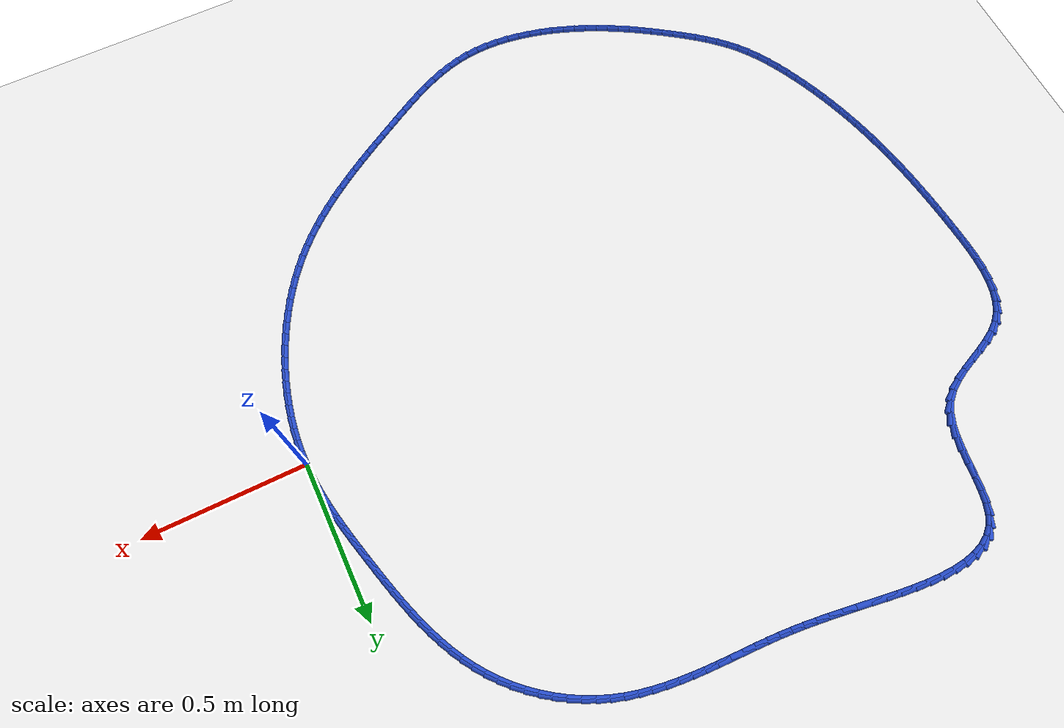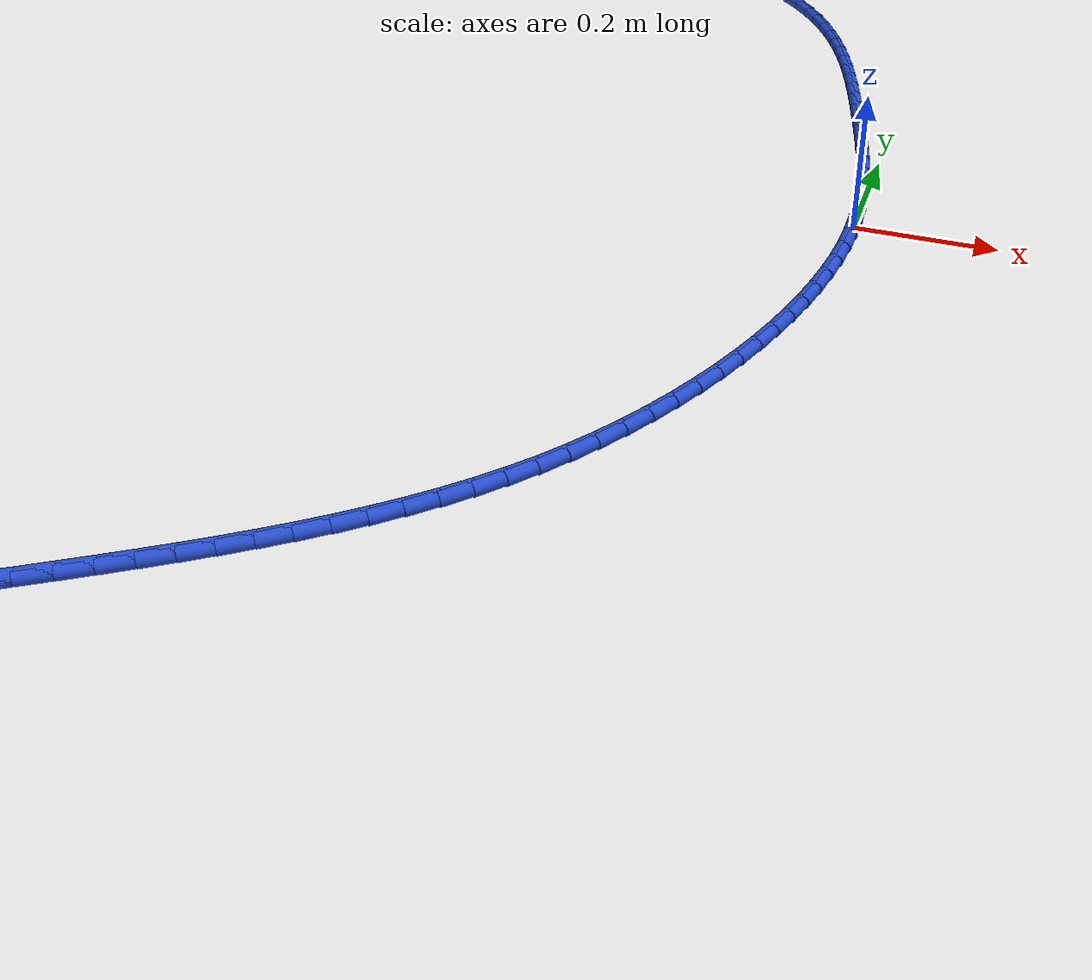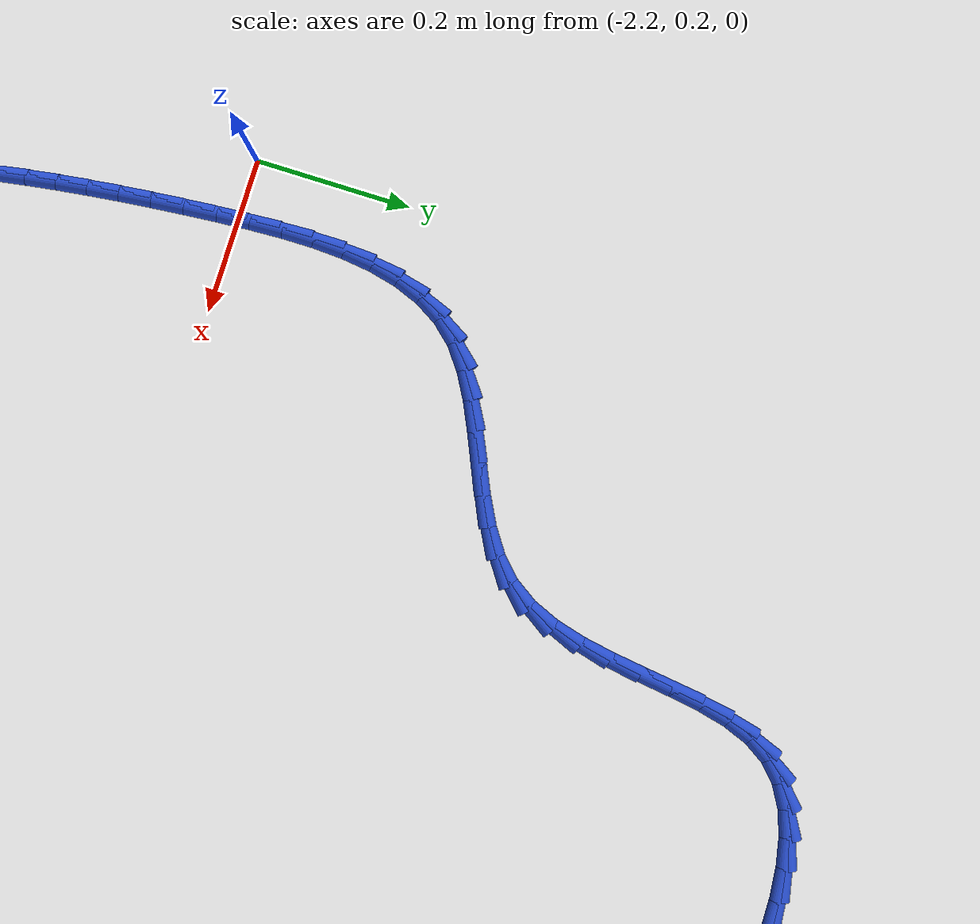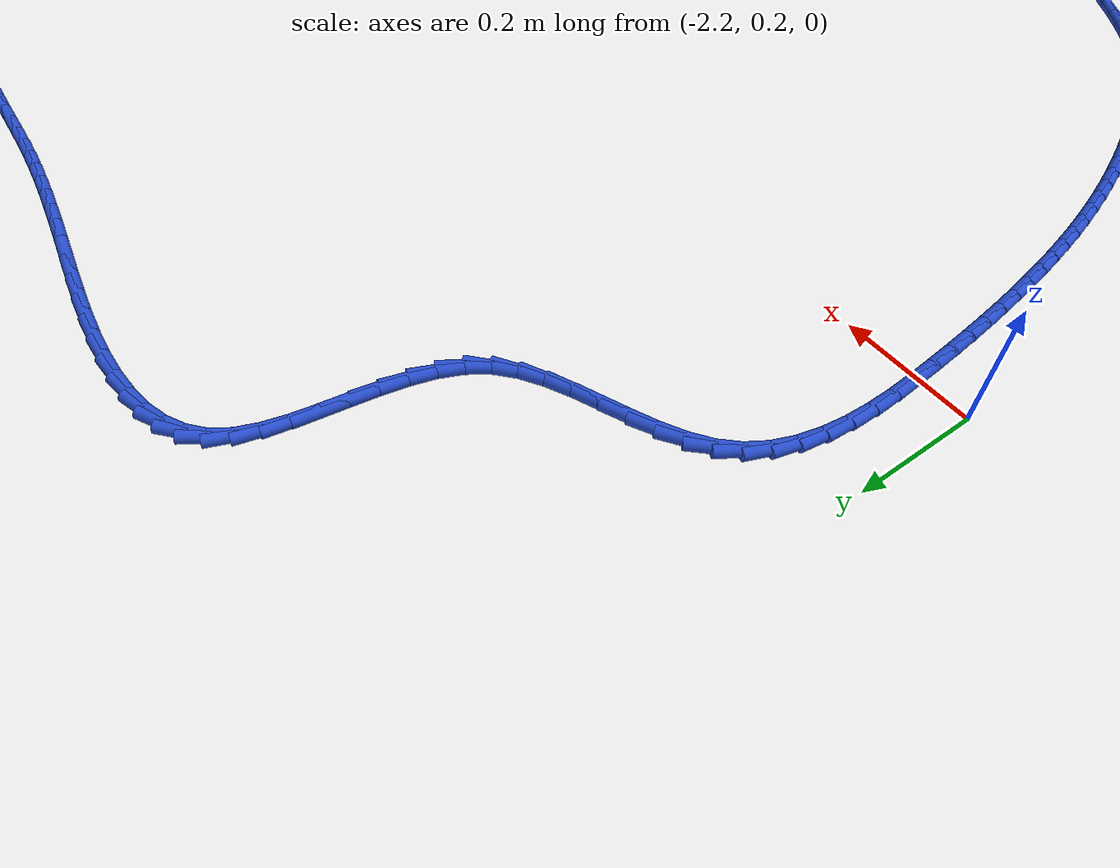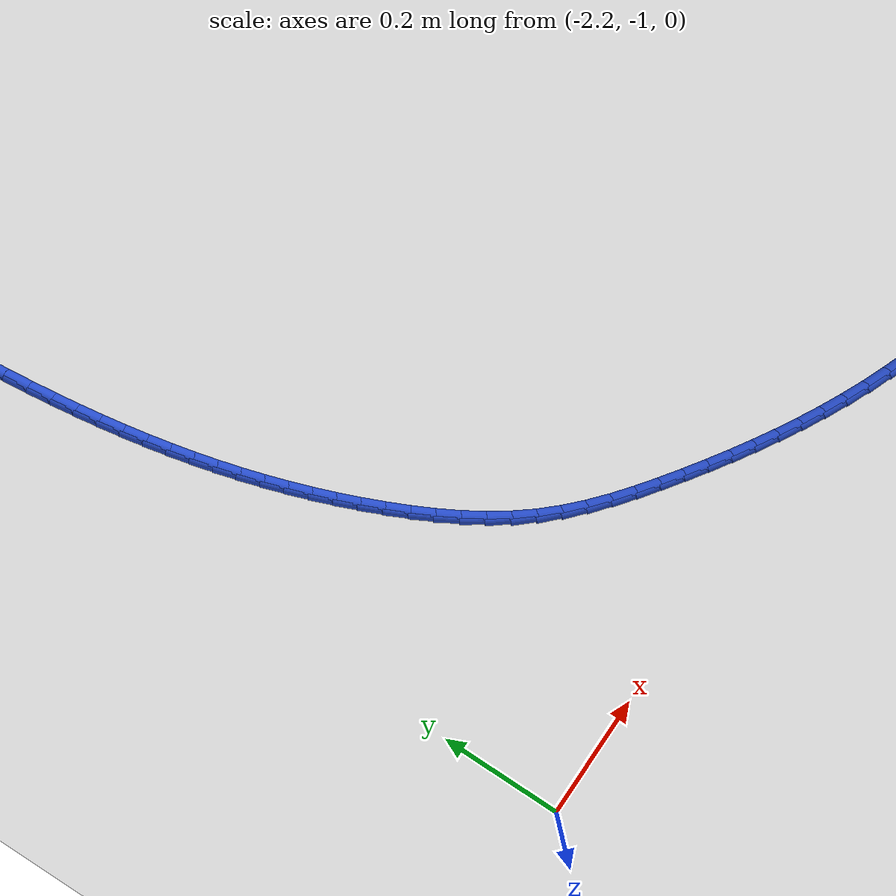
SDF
<sdf version="1.6">
 <world name="default">
  <light name="sun" type="directional">
   <pose>0 0 10 0 -0 0</pose>
   <diffuse>0.8 0.8 0.8 1</diffuse>
   <specular>0.2 0.2 0.2 1</specular>
   <attenuation>
    <range>1000</range>
    <constant>0.9</constant>
    <linear>0.01</linear>
    <quadratic>0.001</quadratic>
   </attenuation>
   <direction>-0.5 0.1 -0.9</direction>
  </light>
  <model name="ground_plane">
   <static>1</static>
   <link name="link">
    <collision name="collision">
     <geometry><plane><normal>0 0 1</normal><size>100 100</size></plane></geometry>
     <surface><friction><ode><mu>100</mu><mu2>50</mu2></ode></friction></surface>
    </collision>
    <visual name="visual">
     <cast_shadows>0</cast_shadows>
     <geometry><plane><normal>0 0 1</normal><size>100 100</size></plane></geometry>
     <material>
      <script><uri>file://media/materials/scripts/gazebo.material</uri><name>Gazebo/WhiteGlow</name></script>
     </material>
    </visual>
   </link>
  </model>
  <gravity>0 0 -9.8</gravity>
  <magnetic_field>6e-06 2.3e-05 -4.2e-05</magnetic_field>
  <atmosphere type="adiabatic"/>
  <physics name="default_physics" default="0" type="ode">
   <max_step_size>0.001</max_step_size>
   <real_time_factor>1</real_time_factor>
   <real_time_update_rate>1000</real_time_update_rate>
  </physics>
  <scene><ambient>0.4 0.4 0.4 1</ambient><background>0.7 0.7 0.7 1</background><shadows>1</shadows></scene>
  <spherical_coordinates>
   <surface_model>EARTH_WGS84</surface_model>
   <latitude_deg>0</latitude_deg>
   <longitude_deg>0</longitude_deg>
   <elevation>0</elevation>
   <heading_deg>0</heading_deg>
  </spherical_coordinates>
  <model name="line">
   <link name="link_0">
    <pose>3.469446951953614e-17 1.6653345369377348e-16 0.01 0 1.57 -1.5247900248946589</pose>
    <collision name="collision">
     <geometry><cylinder><radius>0.01</radius><length>0.08</length></cylinder></geometry>
    </collision>
    <visual name="visual">
     <material>
      <script><name>Gazebo/Blue</name><uri>file://media/materials/scripts/gazebo.material</uri></script>
     </material>
     <geometry><cylinder><radius>0.01</radius><length>0.08</length></cylinder></geometry>
    </visual>
   </link>
   <link name="link_1">
    <pose>-0.0017331883474911327 0.03764626350921732 0.01 0 1.57 -1.4815289747677483</pose>
    <collision name="collision">
     <geometry><cylinder><radius>0.01</radius><length>0.08</length></cylinder></geometry>
    </collision>
    <visual name="visual">
     <material>
      <script><name>Gazebo/Blue</name><uri>file://media/materials/scripts/gazebo.material</uri></script>
     </material>
     <geometry><cylinder><radius>0.01</radius><length>0.08</length></cylinder></geometry>
    </visual>
   </link>
   <link name="link_2">
    <pose>-0.005092713649914606 0.07518066823448695 0.01 0 1.57 -1.4431858875743346</pose>
    <collision name="collision">
     <geometry><cylinder><radius>0.01</radius><length>0.08</length></cylinder></geometry>
    </collision>
    <visual name="visual">
     <material>
      <script><name>Gazebo/Blue</name><uri>file://media/materials/scripts/gazebo.material</uri></script>
     </material>
     <geometry><cylinder><radius>0.01</radius><length>0.08</length></cylinder></geometry>
    </visual>
   </link>
   <link name="link_3">
    <pose>-0.009897221894903094 0.11262588327635743 0.01 0 1.57 -1.4098582267727047</pose>
    <collision name="collision">
     <geometry><cylinder><radius>0.01</radius><length>0.08</length></cylinder></geometry>
    </collision>
    <visual name="visual">
     <material>
      <script><name>Gazebo/Blue</name><uri>file://media/materials/scripts/gazebo.material</uri></script>
     </material>
     <geometry><cylinder><radius>0.01</radius><length>0.08</length></cylinder></geometry>
    </visual>
   </link>
   <link name="link_4">
    <pose>-0.015965359070089336 0.1500045777353774 0.01 0 1.57 -1.3815666401645523</pose>
    <collision name="collision">
     <geometry><cylinder><radius>0.01</radius><length>0.08</length></cylinder></geometry>
    </collision>
    <visual name="visual">
     <material>
      <script><name>Gazebo/Blue</name><uri>file://media/materials/scripts/gazebo.material</uri></script>
     </material>
     <geometry><cylinder><radius>0.01</radius><length>0.08</length></cylinder></geometry>
    </visual>
   </link>
   <link name="link_5">
    <pose>-0.023115771163106008 0.18733942071209506 0.01 0 1.57 -1.3582800927733782</pose>
    <collision name="collision">
     <geometry><cylinder><radius>0.01</radius><length>0.08</length></cylinder></geometry>
    </collision>
    <visual name="visual">
     <material>
      <script><name>Gazebo/Blue</name><uri>file://media/materials/scripts/gazebo.material</uri></script>
     </material>
     <geometry><cylinder><radius>0.01</radius><length>0.08</length></cylinder></geometry>
    </visual>
   </link>
   <link name="link_6">
    <pose>-0.031167104161585864 0.22465308130705897 0.01 0 1.57 -1.3399376308576463</pose>
    <collision name="collision">
     <geometry><cylinder><radius>0.01</radius><length>0.08</length></cylinder></geometry>
    </collision>
    <visual name="visual">
     <material>
      <script><name>Gazebo/Blue</name><uri>file://media/materials/scripts/gazebo.material</uri></script>
     </material>
     <geometry><cylinder><radius>0.01</radius><length>0.08</length></cylinder></geometry>
    </visual>
   </link>
   <link name="link_7">
    <pose>-0.0399380040531616 0.2619682286208176 0.01 0 1.57 -1.3264658921392016</pose>
    <collision name="collision">
     <geometry><cylinder><radius>0.01</radius><length>0.08</length></cylinder></geometry>
    </collision>
    <visual name="visual">
     <material>
      <script><name>Gazebo/Blue</name><uri>file://media/materials/scripts/gazebo.material</uri></script>
     </material>
     <geometry><cylinder><radius>0.01</radius><length>0.08</length></cylinder></geometry>
    </visual>
   </link>
   <link name="link_8">
    <pose>-0.049247116825465925 0.29930753175391933 0.01 0 1.57 -1.317792243191467</pose>
    <collision name="collision">
     <geometry><cylinder><radius>0.01</radius><length>0.08</length></cylinder></geometry>
    </collision>
    <visual name="visual">
     <material>
      <script><name>Gazebo/Blue</name><uri>file://media/materials/scripts/gazebo.material</uri></script>
     </material>
     <geometry><cylinder><radius>0.01</radius><length>0.08</length></cylinder></geometry>
    </visual>
   </link>
   <link name="link_9">
    <pose>-0.05891308846613158 0.3366936598069126 0.01 0 1.57 -1.3128598890382424</pose>
    <collision name="collision">
     <geometry><cylinder><radius>0.01</radius><length>0.08</length></cylinder></geometry>
    </collision>
    <visual name="visual">
     <material>
      <script><name>Gazebo/Blue</name><uri>file://media/materials/scripts/gazebo.material</uri></script>
     </material>
     <geometry><cylinder><radius>0.01</radius><length>0.08</length></cylinder></geometry>
    </visual>
   </link>
   <link name="link_10">
    <pose>-0.06879055258570649 0.3741347953621865 0.01 0 1.57 -1.3055094849972249</pose>
    <collision name="collision">
     <geometry><cylinder><radius>0.01</radius><length>0.08</length></cylinder></geometry>
    </collision>
    <visual name="visual">
     <material>
      <script><name>Gazebo/Blue</name><uri>file://media/materials/scripts/gazebo.material</uri></script>
     </material>
     <geometry><cylinder><radius>0.01</radius><length>0.08</length></cylinder></geometry>
    </visual>
   </link>
   <link name="link_11">
    <pose>-0.07895587333172596 0.41154986521943626 0.01 0 1.57 -1.2933846026535858</pose>
    <collision name="collision">
     <geometry><cylinder><radius>0.01</radius><length>0.08</length></cylinder></geometry>
    </collision>
    <visual name="visual">
     <material>
      <script><name>Gazebo/Blue</name><uri>file://media/materials/scripts/gazebo.material</uri></script>
     </material>
     <geometry><cylinder><radius>0.01</radius><length>0.08</length></cylinder></geometry>
    </visual>
   </link>
   <link name="link_12">
    <pose>-0.08956978862036148 0.44882383221984856 0.01 0 1.57 -1.2764155680008045</pose>
    <collision name="collision">
     <geometry><cylinder><radius>0.01</radius><length>0.08</length></cylinder></geometry>
    </collision>
    <visual name="visual">
     <material>
      <script><name>Gazebo/Blue</name><uri>file://media/materials/scripts/gazebo.material</uri></script>
     </material>
     <geometry><cylinder><radius>0.01</radius><length>0.08</length></cylinder></geometry>
    </visual>
   </link>
   <link name="link_13">
    <pose>-0.10079320085683027 0.48584159299091306 0.01 0 1.57 -1.2544996602432215</pose>
    <collision name="collision">
     <geometry><cylinder><radius>0.01</radius><length>0.08</length></cylinder></geometry>
    </collision>
    <visual name="visual">
     <material>
      <script><name>Gazebo/Blue</name><uri>file://media/materials/scripts/gazebo.material</uri></script>
     </material>
     <geometry><cylinder><radius>0.01</radius><length>0.08</length></cylinder></geometry>
    </visual>
   </link>
   <link name="link_14">
    <pose>-0.11278701244634962 0.5224880441601196 0.01 0 1.57 -1.2275071825183512</pose>
    <collision name="collision">
     <geometry><cylinder><radius>0.01</radius><length>0.08</length></cylinder></geometry>
    </collision>
    <visual name="visual">
     <material>
      <script><name>Gazebo/Blue</name><uri>file://media/materials/scripts/gazebo.material</uri></script>
     </material>
     <geometry><cylinder><radius>0.01</radius><length>0.08</length></cylinder></geometry>
    </visual>
   </link>
   <link name="link_15">
    <pose>-0.12571212579413674 0.558648082354958 0.01 0 1.57 -1.1952963206039646</pose>
    <collision name="collision">
     <geometry><cylinder><radius>0.01</radius><length>0.08</length></cylinder></geometry>
    </collision>
    <visual name="visual">
     <material>
      <script><name>Gazebo/Blue</name><uri>file://media/materials/scripts/gazebo.material</uri></script>
     </material>
     <geometry><cylinder><radius>0.01</radius><length>0.08</length></cylinder></geometry>
    </visual>
   </link>
   <link name="link_16">
    <pose>-0.13972944330540882 0.594206604202918 0.01 0 1.57 -1.1577334255400793</pose>
    <collision name="collision">
     <geometry><cylinder><radius>0.01</radius><length>0.08</length></cylinder></geometry>
    </collision>
    <visual name="visual">
     <material>
      <script><name>Gazebo/Blue</name><uri>file://media/materials/scripts/gazebo.material</uri></script>
     </material>
     <geometry><cylinder><radius>0.01</radius><length>0.08</length></cylinder></geometry>
    </visual>
   </link>
   <link name="link_17">
    <pose>-0.15499986738538307 0.6290485063314891 0.01 0 1.57 -1.1147197260796398</pose>
    <collision name="collision">
     <geometry><cylinder><radius>0.01</radius><length>0.08</length></cylinder></geometry>
    </collision>
    <visual name="visual">
     <material>
      <script><name>Gazebo/Blue</name><uri>file://media/materials/scripts/gazebo.material</uri></script>
     </material>
     <geometry><cylinder><radius>0.01</radius><length>0.08</length></cylinder></geometry>
    </visual>
   </link>
   <link name="link_18">
    <pose>-0.17168430043927685 0.6630586853681615 0.01 0 1.57 -1.0662248075592544</pose>
    <collision name="collision">
     <geometry><cylinder><radius>0.01</radius><length>0.08</length></cylinder></geometry>
    </collision>
    <visual name="visual">
     <material>
      <script><name>Gazebo/Blue</name><uri>file://media/materials/scripts/gazebo.material</uri></script>
     </material>
     <geometry><cylinder><radius>0.01</radius><length>0.08</length></cylinder></geometry>
    </visual>
   </link>
   <link name="link_19">
    <pose>-0.18994364487230728 0.6961220379404246 0.01 0 1.57 -1.0123258024327875</pose>
    <collision name="collision">
     <geometry><cylinder><radius>0.01</radius><length>0.08</length></cylinder></geometry>
    </collision>
    <visual name="visual">
     <material>
      <script><name>Gazebo/Blue</name><uri>file://media/materials/scripts/gazebo.material</uri></script>
     </material>
     <geometry><cylinder><radius>0.01</radius><length>0.08</length></cylinder></geometry>
    </visual>
   </link>
   <link name="link_20">
    <pose>-0.20993880308969165 0.7281234606757686 0.01 0 1.57 -0.953249003512818</pose>
    <collision name="collision">
     <geometry><cylinder><radius>0.01</radius><length>0.08</length></cylinder></geometry>
    </collision>
    <visual name="visual">
     <material>
      <script><name>Gazebo/Blue</name><uri>file://media/materials/scripts/gazebo.material</uri></script>
     </material>
     <geometry><cylinder><radius>0.01</radius><length>0.08</length></cylinder></geometry>
    </visual>
   </link>
   <link name="link_21">
    <pose>-0.2318306774966472 0.7589478502016829 0.01 0 1.57 -0.8898010197236053</pose>
    <collision name="collision">
     <geometry><cylinder><radius>0.01</radius><length>0.08</length></cylinder></geometry>
    </collision>
    <visual name="visual">
     <material>
      <script><name>Gazebo/Blue</name><uri>file://media/materials/scripts/gazebo.material</uri></script>
     </material>
     <geometry><cylinder><radius>0.01</radius><length>0.08</length></cylinder></geometry>
    </visual>
   </link>
   <link name="link_22">
    <pose>-0.25576040202475725 0.7884794588531318 0.01 0 1.57 -0.8260626586561787</pose>
    <collision name="collision">
     <geometry><cylinder><radius>0.01</radius><length>0.08</length></cylinder></geometry>
    </collision>
    <visual name="visual">
     <material>
      <script><name>Gazebo/Blue</name><uri>file://media/materials/scripts/gazebo.material</uri></script>
     </material>
     <geometry><cylinder><radius>0.01</radius><length>0.08</length></cylinder></geometry>
    </visual>
   </link>
   <link name="link_23">
    <pose>-0.28167875084354826 0.8165963347747986 0.01 0 1.57 -0.7637797927869033</pose>
    <collision name="collision">
     <geometry><cylinder><radius>0.01</radius><length>0.08</length></cylinder></geometry>
    </collision>
    <visual name="visual">
     <material>
      <script><name>Gazebo/Blue</name><uri>file://media/materials/scripts/gazebo.material</uri></script>
     </material>
     <geometry><cylinder><radius>0.01</radius><length>0.08</length></cylinder></geometry>
    </visual>
   </link>
   <link name="link_24">
    <pose>-0.30943014430683297 0.8431730598362355 0.01 0 1.57 -0.702469948848878</pose>
    <collision name="collision">
     <geometry><cylinder><radius>0.01</radius><length>0.08</length></cylinder></geometry>
    </collision>
    <visual name="visual">
     <material>
      <script><name>Gazebo/Blue</name><uri>file://media/materials/scripts/gazebo.material</uri></script>
     </material>
     <geometry><cylinder><radius>0.01</radius><length>0.08</length></cylinder></geometry>
    </visual>
   </link>
   <link name="link_25">
    <pose>-0.3388578419103098 0.8680841780723975 0.01 0 1.57 -0.6416291802982655</pose>
    <collision name="collision">
     <geometry><cylinder><radius>0.01</radius><length>0.08</length></cylinder></geometry>
    </collision>
    <visual name="visual">
     <material>
      <script><name>Gazebo/Blue</name><uri>file://media/materials/scripts/gazebo.material</uri></script>
     </material>
     <geometry><cylinder><radius>0.01</radius><length>0.08</length></cylinder></geometry>
    </visual>
   </link>
   <link name="link_26">
    <pose>-0.36980510314967685 0.8912042335182397 0.01 0 1.57 -0.5807573015856039</pose>
    <collision name="collision">
     <geometry><cylinder><radius>0.01</radius><length>0.08</length></cylinder></geometry>
    </collision>
    <visual name="visual">
     <material>
      <script><name>Gazebo/Blue</name><uri>file://media/materials/scripts/gazebo.material</uri></script>
     </material>
     <geometry><cylinder><radius>0.01</radius><length>0.08</length></cylinder></geometry>
    </visual>
   </link>
   <link name="link_27">
    <pose>-0.4021151875206324 0.9124077702087185 0.01 0 1.57 -0.5193590099628549</pose>
    <collision name="collision">
     <geometry><cylinder><radius>0.01</radius><length>0.08</length></cylinder></geometry>
    </collision>
    <visual name="visual">
     <material>
      <script><name>Gazebo/Blue</name><uri>file://media/materials/scripts/gazebo.material</uri></script>
     </material>
     <geometry><cylinder><radius>0.01</radius><length>0.08</length></cylinder></geometry>
    </visual>
   </link>
   <link name="link_28">
    <pose>-0.43563135451887486 0.9315693321787886 0.01 0 1.57 -0.45694529368833253</pose>
    <collision name="collision">
     <geometry><cylinder><radius>0.01</radius><length>0.08</length></cylinder></geometry>
    </collision>
    <visual name="visual">
     <material>
      <script><name>Gazebo/Blue</name><uri>file://media/materials/scripts/gazebo.material</uri></script>
     </material>
     <geometry><cylinder><radius>0.01</radius><length>0.08</length></cylinder></geometry>
    </visual>
   </link>
   <link name="link_29">
    <pose>-0.4701968636401025 0.9485634634634056 0.01 0 1.57 -0.39303638831993953</pose>
    <collision name="collision">
     <geometry><cylinder><radius>0.01</radius><length>0.08</length></cylinder></geometry>
    </collision>
    <visual name="visual">
     <material>
      <script><name>Gazebo/Blue</name><uri>file://media/materials/scripts/gazebo.material</uri></script>
     </material>
     <geometry><cylinder><radius>0.01</radius><length>0.08</length></cylinder></geometry>
    </visual>
   </link>
   <link name="link_30">
    <pose>-0.5056549743800133 0.9632647080975247 0.01 0 1.57 -0.3280408990402076</pose>
    <collision name="collision">
     <geometry><cylinder><radius>0.01</radius><length>0.08</length></cylinder></geometry>
    </collision>
    <visual name="visual">
     <material>
      <script><name>Gazebo/Blue</name><uri>file://media/materials/scripts/gazebo.material</uri></script>
     </material>
     <geometry><cylinder><radius>0.01</radius><length>0.08</length></cylinder></geometry>
    </visual>
   </link>
   <link name="link_31">
    <pose>-0.5418543080608096 0.9755846946069876 0.01 0 1.57 -0.26750801333935326</pose>
    <collision name="collision">
     <geometry><cylinder><radius>0.01</radius><length>0.08</length></cylinder></geometry>
    </collision>
    <visual name="visual">
     <material>
      <script><name>Gazebo/Blue</name><uri>file://media/materials/scripts/gazebo.material</uri></script>
     </material>
     <geometry><cylinder><radius>0.01</radius><length>0.08</length></cylinder></geometry>
    </visual>
   </link>
   <link name="link_32">
    <pose>-0.5786785212308259 0.9856773688554341 0.01 0 1.57 -0.2140031497154433</pose>
    <collision name="collision">
     <geometry><cylinder><radius>0.01</radius><length>0.08</length></cylinder></geometry>
    </collision>
    <visual name="visual">
     <material>
      <script><name>Gazebo/Blue</name><uri>file://media/materials/scripts/gazebo.material</uri></script>
     </material>
     <geometry><cylinder><radius>0.01</radius><length>0.08</length></cylinder></geometry>
    </visual>
   </link>
   <link name="link_33">
    <pose>-0.6160253407426954 0.9937939924385889 0.01 0 1.57 -0.16766114630379586</pose>
    <collision name="collision">
     <geometry><cylinder><radius>0.01</radius><length>0.08</length></cylinder></geometry>
    </collision>
    <visual name="visual">
     <material>
      <script><name>Gazebo/Blue</name><uri>file://media/materials/scripts/gazebo.material</uri></script>
     </material>
     <geometry><cylinder><radius>0.01</radius><length>0.08</length></cylinder></geometry>
    </visual>
   </link>
   <link name="link_34">
    <pose>-0.6537925314790798 1.0001860899827402 0.01 0 1.57 -0.12844875463617564</pose>
    <collision name="collision">
     <geometry><cylinder><radius>0.01</radius><length>0.08</length></cylinder></geometry>
    </collision>
    <visual name="visual">
     <material>
      <script><name>Gazebo/Blue</name><uri>file://media/materials/scripts/gazebo.material</uri></script>
     </material>
     <geometry><cylinder><radius>0.01</radius><length>0.08</length></cylinder></geometry>
    </visual>
   </link>
   <link name="link_35">
    <pose>-0.6918778583226416 1.0051051861141758 0.01 0 1.57 -0.09624223592973855</pose>
    <collision name="collision">
     <geometry><cylinder><radius>0.01</radius><length>0.08</length></cylinder></geometry>
    </collision>
    <visual name="visual">
     <material>
      <script><name>Gazebo/Blue</name><uri>file://media/materials/scripts/gazebo.material</uri></script>
     </material>
     <geometry><cylinder><radius>0.01</radius><length>0.08</length></cylinder></geometry>
    </visual>
   </link>
   <link name="link_36">
    <pose>-0.7301790861560422 1.0088028054591833 0.01 0 1.57 -0.07088648814556454</pose>
    <collision name="collision">
     <geometry><cylinder><radius>0.01</radius><length>0.08</length></cylinder></geometry>
    </collision>
    <visual name="visual">
     <material>
      <script><name>Gazebo/Blue</name><uri>file://media/materials/scripts/gazebo.material</uri></script>
     </material>
     <geometry><cylinder><radius>0.01</radius><length>0.08</length></cylinder></geometry>
    </visual>
   </link>
   <link name="link_37">
    <pose>-0.7685939798619437 1.0115304726440508 0.01 0 1.57 -0.05224052936037292</pose>
    <collision name="collision">
     <geometry><cylinder><radius>0.01</radius><length>0.08</length></cylinder></geometry>
    </collision>
    <visual name="visual">
     <material>
      <script><name>Gazebo/Blue</name><uri>file://media/materials/scripts/gazebo.material</uri></script>
     </material>
     <geometry><cylinder><radius>0.01</radius><length>0.08</length></cylinder></geometry>
    </visual>
   </link>
   <link name="link_38">
    <pose>-0.8070203043230079 1.0135397122950667 0.01 0 1.57 -0.04021088989289936</pose>
    <collision name="collision">
     <geometry><cylinder><radius>0.01</radius><length>0.08</length></cylinder></geometry>
    </collision>
    <visual name="visual">
     <material>
      <script><name>Gazebo/Blue</name><uri>file://media/materials/scripts/gazebo.material</uri></script>
     </material>
     <geometry><cylinder><radius>0.01</radius><length>0.08</length></cylinder></geometry>
    </visual>
   </link>
   <link name="link_39">
    <pose>-0.8453558244218969 1.0150820490385184 0.01 0 1.57 -0.03477549139845413</pose>
    <collision name="collision">
     <geometry><cylinder><radius>0.01</radius><length>0.08</length></cylinder></geometry>
    </collision>
    <visual name="visual">
     <material>
      <script><name>Gazebo/Blue</name><uri>file://media/materials/scripts/gazebo.material</uri></script>
     </material>
     <geometry><cylinder><radius>0.01</radius><length>0.08</length></cylinder></geometry>
    </visual>
   </link>
   <link name="link_40">
    <pose>-0.8834983050412724 1.0164090075006937 0.01 0 1.57 -0.03600043501181921</pose>
    <collision name="collision">
     <geometry><cylinder><radius>0.01</radius><length>0.08</length></cylinder></geometry>
    </collision>
    <visual name="visual">
     <material>
      <script><name>Gazebo/Blue</name><uri>file://media/materials/scripts/gazebo.material</uri></script>
     </material>
     <geometry><cylinder><radius>0.01</radius><length>0.08</length></cylinder></geometry>
    </visual>
   </link>
   <link name="link_41">
    <pose>-0.9213455110637964 1.017772112307881 0.01 0 1.57 -0.04405130125781281</pose>
    <collision name="collision">
     <geometry><cylinder><radius>0.01</radius><length>0.08</length></cylinder></geometry>
    </collision>
    <visual name="visual">
     <material>
      <script><name>Gazebo/Blue</name><uri>file://media/materials/scripts/gazebo.material</uri></script>
     </material>
     <geometry><cylinder><radius>0.01</radius><length>0.08</length></cylinder></geometry>
    </visual>
   </link>
   <link name="link_42">
    <pose>-0.9587952073721308 1.0194228880863678 0.01 0 1.57 -0.0591958668253946</pose>
    <collision name="collision">
     <geometry><cylinder><radius>0.01</radius><length>0.08</length></cylinder></geometry>
    </collision>
    <visual name="visual">
     <material>
      <script><name>Gazebo/Blue</name><uri>file://media/materials/scripts/gazebo.material</uri></script>
     </material>
     <geometry><cylinder><radius>0.01</radius><length>0.08</length></cylinder></geometry>
    </visual>
   </link>
   <link name="link_43">
    <pose>-0.9957453442663211 1.021612741926129 0.01 0 1.57 -0.0795985463917148</pose>
    <collision name="collision">
     <geometry><cylinder><radius>0.01</radius><length>0.08</length></cylinder></geometry>
    </collision>
    <visual name="visual">
     <material>
      <script><name>Gazebo/Blue</name><uri>file://media/materials/scripts/gazebo.material</uri></script>
     </material>
     <geometry><cylinder><radius>0.01</radius><length>0.08</length></cylinder></geometry>
    </visual>
   </link>
   <link name="link_44">
    <pose>-1.0322072621542264 1.0245212027849324 0.01 0 1.57 -0.0992207175375797</pose>
    <collision name="collision">
     <geometry><cylinder><radius>0.01</radius><length>0.08</length></cylinder></geometry>
    </collision>
    <visual name="visual">
     <material>
      <script><name>Gazebo/Blue</name><uri>file://media/materials/scripts/gazebo.material</uri></script>
     </material>
     <geometry><cylinder><radius>0.01</radius><length>0.08</length></cylinder></geometry>
    </visual>
   </link>
   <link name="link_45">
    <pose>-1.068498215510047 1.0281338803084556 0.01 0 1.57 -0.11649737409116405</pose>
    <collision name="collision">
     <geometry><cylinder><radius>0.01</radius><length>0.08</length></cylinder></geometry>
    </collision>
    <visual name="visual">
     <material>
      <script><name>Gazebo/Blue</name><uri>file://media/materials/scripts/gazebo.material</uri></script>
     </material>
     <geometry><cylinder><radius>0.01</radius><length>0.08</length></cylinder></geometry>
    </visual>
   </link>
   <link name="link_46">
    <pose>-1.1049865324952386 1.032404008467679 0.01 0 1.57 -0.13096760363867704</pose>
    <collision name="collision">
     <geometry><cylinder><radius>0.01</radius><length>0.08</length></cylinder></geometry>
    </collision>
    <visual name="visual">
     <material>
      <script><name>Gazebo/Blue</name><uri>file://media/materials/scripts/gazebo.material</uri></script>
     </material>
     <geometry><cylinder><radius>0.01</radius><length>0.08</length></cylinder></geometry>
    </visual>
   </link>
   <link name="link_47">
    <pose>-1.142040541271253 1.0372848212335812 0.01 0 1.57 -0.1423580298324307</pose>
    <collision name="collision">
     <geometry><cylinder><radius>0.01</radius><length>0.08</length></cylinder></geometry>
    </collision>
    <visual name="visual">
     <material>
      <script><name>Gazebo/Blue</name><uri>file://media/materials/scripts/gazebo.material</uri></script>
     </material>
     <geometry><cylinder><radius>0.01</radius><length>0.08</length></cylinder></geometry>
    </visual>
   </link>
   <link name="link_48">
    <pose>-1.180028569999545 1.0427295525771423 0.01 0 1.57 -0.15059028054810106</pose>
    <collision name="collision">
     <geometry><cylinder><radius>0.01</radius><length>0.08</length></cylinder></geometry>
    </collision>
    <visual name="visual">
     <material>
      <script><name>Gazebo/Blue</name><uri>file://media/materials/scripts/gazebo.material</uri></script>
     </material>
     <geometry><cylinder><radius>0.01</radius><length>0.08</length></cylinder></geometry>
    </visual>
   </link>
   <link name="link_49">
    <pose>-1.2193189468415688 1.048691436469342 0.01 0 1.57 -0.1557584775787211</pose>
    <collision name="collision">
     <geometry><cylinder><radius>0.01</radius><length>0.08</length></cylinder></geometry>
    </collision>
    <visual name="visual">
     <material>
      <script><name>Gazebo/Blue</name><uri>file://media/materials/scripts/gazebo.material</uri></script>
     </material>
     <geometry><cylinder><radius>0.01</radius><length>0.08</length></cylinder></geometry>
    </visual>
   </link>
   <link name="link_50">
    <pose>-1.260279589269334 1.0551235035889648 0.01 0 1.57 -0.1561284405691426</pose>
    <collision name="collision">
     <geometry><cylinder><radius>0.01</radius><length>0.08</length></cylinder></geometry>
    </collision>
    <visual name="visual">
     <material>
      <script><name>Gazebo/Blue</name><uri>file://media/materials/scripts/gazebo.material</uri></script>
     </material>
     <geometry><cylinder><radius>0.01</radius><length>0.08</length></cylinder></geometry>
    </visual>
   </link>
   <link name="link_51">
    <pose>-1.303021134423855 1.0618514302744986 0.01 0 1.57 -0.14697952493277214</pose>
    <collision name="collision">
     <geometry><cylinder><radius>0.01</radius><length>0.08</length></cylinder></geometry>
    </collision>
    <visual name="visual">
     <material>
      <script><name>Gazebo/Blue</name><uri>file://media/materials/scripts/gazebo.material</uri></script>
     </material>
     <geometry><cylinder><radius>0.01</radius><length>0.08</length></cylinder></geometry>
    </visual>
   </link>
   <link name="link_52">
    <pose>-1.3469576983085867 1.0683561133407367 0.01 0 1.57 -0.12769859646323264</pose>
    <collision name="collision">
     <geometry><cylinder><radius>0.01</radius><length>0.08</length></cylinder></geometry>
    </collision>
    <visual name="visual">
     <material>
      <script><name>Gazebo/Blue</name><uri>file://media/materials/scripts/gazebo.material</uri></script>
     </material>
     <geometry><cylinder><radius>0.01</radius><length>0.08</length></cylinder></geometry>
    </visual>
   </link>
   <link name="link_53">
    <pose>-1.3913866778266022 1.0740606733862677 0.01 0 1.57 -0.09755626341747135</pose>
    <collision name="collision">
     <geometry><cylinder><radius>0.01</radius><length>0.08</length></cylinder></geometry>
    </collision>
    <visual name="visual">
     <material>
      <script><name>Gazebo/Blue</name><uri>file://media/materials/scripts/gazebo.material</uri></script>
     </material>
     <geometry><cylinder><radius>0.01</radius><length>0.08</length></cylinder></geometry>
    </visual>
   </link>
   <link name="link_54">
    <pose>-1.4356054698809773 1.0783882310096802 0.01 0 1.57 -0.05475691353478836</pose>
    <collision name="collision">
     <geometry><cylinder><radius>0.01</radius><length>0.08</length></cylinder></geometry>
    </collision>
    <visual name="visual">
     <material>
      <script><name>Gazebo/Blue</name><uri>file://media/materials/scripts/gazebo.material</uri></script>
     </material>
     <geometry><cylinder><radius>0.01</radius><length>0.08</length></cylinder></geometry>
    </visual>
   </link>
   <link name="link_55">
    <pose>-1.4789114713747853 1.080761906809562 0.01 0 1.57 0.0037678673888654627</pose>
    <collision name="collision">
     <geometry><cylinder><radius>0.01</radius><length>0.08</length></cylinder></geometry>
    </collision>
    <visual name="visual">
     <material>
      <script><name>Gazebo/Blue</name><uri>file://media/materials/scripts/gazebo.material</uri></script>
     </material>
     <geometry><cylinder><radius>0.01</radius><length>0.08</length></cylinder></geometry>
    </visual>
   </link>
   <link name="link_56">
    <pose>-1.5206020792110997 1.0806048213845014 0.01 0 1.57 0.08272945218387376</pose>
    <collision name="collision">
     <geometry><cylinder><radius>0.01</radius><length>0.08</length></cylinder></geometry>
    </collision>
    <visual name="visual">
     <material>
      <script><name>Gazebo/Blue</name><uri>file://media/materials/scripts/gazebo.material</uri></script>
     </material>
     <geometry><cylinder><radius>0.01</radius><length>0.08</length></cylinder></geometry>
    </visual>
   </link>
   <link name="link_57">
    <pose>-1.559974690292995 1.0773400953330863 0.01 0 1.57 0.18888648234141306</pose>
    <collision name="collision">
     <geometry><cylinder><radius>0.01</radius><length>0.08</length></cylinder></geometry>
    </collision>
    <visual name="visual">
     <material>
      <script><name>Gazebo/Blue</name><uri>file://media/materials/scripts/gazebo.material</uri></script>
     </material>
     <geometry><cylinder><radius>0.01</radius><length>0.08</length></cylinder></geometry>
    </visual>
   </link>
   <link name="link_58">
    <pose>-1.5963267015235463 1.0703908492539054 0.01 0 1.57 0.3309451182031308</pose>
    <collision name="collision">
     <geometry><cylinder><radius>0.01</radius><length>0.08</length></cylinder></geometry>
    </collision>
    <visual name="visual">
     <material>
      <script><name>Gazebo/Blue</name><uri>file://media/materials/scripts/gazebo.material</uri></script>
     </material>
     <geometry><cylinder><radius>0.01</radius><length>0.08</length></cylinder></geometry>
    </visual>
   </link>
   <link name="link_59">
    <pose>-1.6289555098058262 1.0591802037455467 0.01 0 1.57 0.5173513586052119</pose>
    <collision name="collision">
     <geometry><cylinder><radius>0.01</radius><length>0.08</length></cylinder></geometry>
    </collision>
    <visual name="visual">
     <material>
      <script><name>Gazebo/Blue</name><uri>file://media/materials/scripts/gazebo.material</uri></script>
     </material>
     <geometry><cylinder><radius>0.01</radius><length>0.08</length></cylinder></geometry>
    </visual>
   </link>
   <link name="link_60">
    <pose>-1.6571585120429095 1.0431312794065986 0.01 0 1.57 0.7492540904446358</pose>
    <collision name="collision">
     <geometry><cylinder><radius>0.01</radius><length>0.08</length></cylinder></geometry>
    </collision>
    <visual name="visual">
     <material>
      <script><name>Gazebo/Blue</name><uri>file://media/materials/scripts/gazebo.material</uri></script>
     </material>
     <geometry><cylinder><radius>0.01</radius><length>0.08</length></cylinder></geometry>
    </visual>
   </link>
   <link name="link_61">
    <pose>-1.6802331051378703 1.0216671968356494 0.01 0 1.57 1.0038397482812604</pose>
    <collision name="collision">
     <geometry><cylinder><radius>0.01</radius><length>0.08</length></cylinder></geometry>
    </collision>
    <visual name="visual">
     <material>
      <script><name>Gazebo/Blue</name><uri>file://media/materials/scripts/gazebo.material</uri></script>
     </material>
     <geometry><cylinder><radius>0.01</radius><length>0.08</length></cylinder></geometry>
    </visual>
   </link>
   <link name="link_62">
    <pose>-1.697628446783464 0.9943453765687943 0.01 0 1.57 1.2059693717743176</pose>
    <collision name="collision">
     <geometry><cylinder><radius>0.01</radius><length>0.08</length></cylinder></geometry>
    </collision>
    <visual name="visual">
     <material>
      <script><name>Gazebo/Blue</name><uri>file://media/materials/scripts/gazebo.material</uri></script>
     </material>
     <geometry><cylinder><radius>0.01</radius><length>0.08</length></cylinder></geometry>
    </visual>
   </link>
   <link name="link_63">
    <pose>-1.7100462121725133 0.9618316481214056 0.01 0 1.57 1.3352409389192696</pose>
    <collision name="collision">
     <geometry><cylinder><radius>0.01</radius><length>0.08</length></cylinder></geometry>
    </collision>
    <visual name="visual">
     <material>
      <script><name>Gazebo/Blue</name><uri>file://media/materials/scripts/gazebo.material</uri></script>
     </material>
     <geometry><cylinder><radius>0.01</radius><length>0.08</length></cylinder></geometry>
    </visual>
   </link>
   <link name="link_64">
    <pose>-1.71880511643042 0.9253378873529671 0.01 0 1.57 1.4086215397395698</pose>
    <collision name="collision">
     <geometry><cylinder><radius>0.01</radius><length>0.08</length></cylinder></geometry>
    </collision>
    <visual name="visual">
     <material>
      <script><name>Gazebo/Blue</name><uri>file://media/materials/scripts/gazebo.material</uri></script>
     </material>
     <geometry><cylinder><radius>0.01</radius><length>0.08</length></cylinder></geometry>
    </visual>
   </link>
   <link name="link_65">
    <pose>-1.7252281983924613 0.8860797963679817 0.01 0 1.57 1.4389815818383545</pose>
    <collision name="collision">
     <geometry><cylinder><radius>0.01</radius><length>0.08</length></cylinder></geometry>
    </collision>
    <visual name="visual">
     <material>
      <script><name>Gazebo/Blue</name><uri>file://media/materials/scripts/gazebo.material</uri></script>
     </material>
     <geometry><cylinder><radius>0.01</radius><length>0.08</length></cylinder></geometry>
    </visual>
   </link>
   <link name="link_66">
    <pose>-1.7306384968939132 0.8452730772709527 0.01 0 1.57 1.4326301883958852</pose>
    <collision name="collision">
     <geometry><cylinder><radius>0.01</radius><length>0.08</length></cylinder></geometry>
    </collision>
    <visual name="visual">
     <material>
      <script><name>Gazebo/Blue</name><uri>file://media/materials/scripts/gazebo.material</uri></script>
     </material>
     <geometry><cylinder><radius>0.01</radius><length>0.08</length></cylinder></geometry>
    </visual>
   </link>
   <link name="link_67">
    <pose>-1.7363590507700524 0.8041334321663843 0.01 0 1.57 1.3901153661759593</pose>
    <collision name="collision">
     <geometry><cylinder><radius>0.01</radius><length>0.08</length></cylinder></geometry>
    </collision>
    <visual name="visual">
     <material>
      <script><name>Gazebo/Blue</name><uri>file://media/materials/scripts/gazebo.material</uri></script>
     </material>
     <geometry><cylinder><radius>0.01</radius><length>0.08</length></cylinder></geometry>
    </visual>
   </link>
   <link name="link_68">
    <pose>-1.743712898856156 0.76387656315878 0.01 0 1.57 1.3069033681007913</pose>
    <collision name="collision">
     <geometry><cylinder><radius>0.01</radius><length>0.08</length></cylinder></geometry>
    </collision>
    <visual name="visual">
     <material>
      <script><name>Gazebo/Blue</name><uri>file://media/materials/scripts/gazebo.material</uri></script>
     </material>
     <geometry><cylinder><radius>0.01</radius><length>0.08</length></cylinder></geometry>
    </visual>
   </link>
   <link name="link_69">
    <pose>-1.7540230799874994 0.7257181723526427 0.01 0 1.57 1.1742670264477717</pose>
    <collision name="collision">
     <geometry><cylinder><radius>0.01</radius><length>0.08</length></cylinder></geometry>
    </collision>
    <visual name="visual">
     <material>
      <script><name>Gazebo/Blue</name><uri>file://media/materials/scripts/gazebo.material</uri></script>
     </material>
     <geometry><cylinder><radius>0.01</radius><length>0.08</length></cylinder></geometry>
    </visual>
   </link>
   <link name="link_70">
    <pose>-1.7686126329993601 0.6908739618524768 0.01 0 1.57 0.9832983461604564</pose>
    <collision name="collision">
     <geometry><cylinder><radius>0.01</radius><length>0.08</length></cylinder></geometry>
    </collision>
    <visual name="visual">
     <material>
      <script><name>Gazebo/Blue</name><uri>file://media/materials/scripts/gazebo.material</uri></script>
     </material>
     <geometry><cylinder><radius>0.01</radius><length>0.08</length></cylinder></geometry>
    </visual>
   </link>
   <link name="link_71">
    <pose>-1.7888017288078237 0.6605571824443162 0.01 0 1.57 0.7639145190522943</pose>
    <collision name="collision">
     <geometry><cylinder><radius>0.01</radius><length>0.08</length></cylinder></geometry>
    </collision>
    <visual name="visual">
     <material>
      <script><name>Gazebo/Blue</name><uri>file://media/materials/scripts/gazebo.material</uri></script>
     </material>
     <geometry><cylinder><radius>0.01</radius><length>0.08</length></cylinder></geometry>
    </visual>
   </link>
   <link name="link_72">
    <pose>-1.8151424737478572 0.6353245912099232 0.01 0 1.57 0.5946269177443292</pose>
    <collision name="collision">
     <geometry><cylinder><radius>0.01</radius><length>0.08</length></cylinder></geometry>
    </collision>
    <visual name="visual">
     <material>
      <script><name>Gazebo/Blue</name><uri>file://media/materials/scripts/gazebo.material</uri></script>
     </material>
     <geometry><cylinder><radius>0.01</radius><length>0.08</length></cylinder></geometry>
    </visual>
   </link>
   <link name="link_73">
    <pose>-1.8463871143754813 0.614194537338674 0.01 0 1.57 0.4843858479858581</pose>
    <collision name="collision">
     <geometry><cylinder><radius>0.01</radius><length>0.08</length></cylinder></geometry>
    </collision>
    <visual name="visual">
     <material>
      <script><name>Gazebo/Blue</name><uri>file://media/materials/scripts/gazebo.material</uri></script>
     </material>
     <geometry><cylinder><radius>0.01</radius><length>0.08</length></cylinder></geometry>
    </visual>
   </link>
   <link name="link_74">
    <pose>-1.8810304181976152 0.5959652929862268 0.01 0 1.57 0.42486942134939903</pose>
    <collision name="collision">
     <geometry><cylinder><radius>0.01</radius><length>0.08</length></cylinder></geometry>
    </collision>
    <visual name="visual">
     <material>
      <script><name>Gazebo/Blue</name><uri>file://media/materials/scripts/gazebo.material</uri></script>
     </material>
     <geometry><cylinder><radius>0.01</radius><length>0.08</length></cylinder></geometry>
    </visual>
   </link>
   <link name="link_75">
    <pose>-1.9175671527211777 0.5794351303082398 0.01 0 1.57 0.4096373216991103</pose>
    <collision name="collision">
     <geometry><cylinder><radius>0.01</radius><length>0.08</length></cylinder></geometry>
    </collision>
    <visual name="visual">
     <material>
      <script><name>Gazebo/Blue</name><uri>file://media/materials/scripts/gazebo.material</uri></script>
     </material>
     <geometry><cylinder><radius>0.01</radius><length>0.08</length></cylinder></geometry>
    </visual>
   </link>
   <link name="link_76">
    <pose>-1.9544920854530885 0.5634023214603715 0.01 0 1.57 0.4372422703397794</pose>
    <collision name="collision">
     <geometry><cylinder><radius>0.01</radius><length>0.08</length></cylinder></geometry>
    </collision>
    <visual name="visual">
     <material>
      <script><name>Gazebo/Blue</name><uri>file://media/materials/scripts/gazebo.material</uri></script>
     </material>
     <geometry><cylinder><radius>0.01</radius><length>0.08</length></cylinder></geometry>
    </visual>
   </link>
   <link name="link_77">
    <pose>-1.9902999839002673 0.5466651385982798 0.01 0 1.57 0.5118483165190343</pose>
    <collision name="collision">
     <geometry><cylinder><radius>0.01</radius><length>0.08</length></cylinder></geometry>
    </collision>
    <visual name="visual">
     <material>
      <script><name>Gazebo/Blue</name><uri>file://media/materials/scripts/gazebo.material</uri></script>
     </material>
     <geometry><cylinder><radius>0.01</radius><length>0.08</length></cylinder></geometry>
    </visual>
   </link>
   <link name="link_78">
    <pose>-2.023485615569633 0.5280218538776233 0.01 0 1.57 0.6425647303919684</pose>
    <collision name="collision">
     <geometry><cylinder><radius>0.01</radius><length>0.08</length></cylinder></geometry>
    </collision>
    <visual name="visual">
     <material>
      <script><name>Gazebo/Blue</name><uri>file://media/materials/scripts/gazebo.material</uri></script>
     </material>
     <geometry><cylinder><radius>0.01</radius><length>0.08</length></cylinder></geometry>
    </visual>
   </link>
   <link name="link_79">
    <pose>-2.052543747968105 0.5062707394540601 0.01 0 1.57 0.8333347192759247</pose>
    <collision name="collision">
     <geometry><cylinder><radius>0.01</radius><length>0.08</length></cylinder></geometry>
    </collision>
    <visual name="visual">
     <material>
      <script><name>Gazebo/Blue</name><uri>file://media/materials/scripts/gazebo.material</uri></script>
     </material>
     <geometry><cylinder><radius>0.01</radius><length>0.08</length></cylinder></geometry>
    </visual>
   </link>
   <link name="link_80">
    <pose>-2.076110308696768 0.4803291069383162 0.01 0 1.57 1.0318248917790673</pose>
    <collision name="collision">
     <geometry><cylinder><radius>0.01</radius><length>0.08</length></cylinder></geometry>
    </collision>
    <visual name="visual">
     <material>
      <script><name>Gazebo/Blue</name><uri>file://media/materials/scripts/gazebo.material</uri></script>
     </material>
     <geometry><cylinder><radius>0.01</radius><length>0.08</length></cylinder></geometry>
    </visual>
   </link>
   <link name="link_81">
    <pose>-2.0941218597656834 0.45021108508482 0.01 0 1.57 1.2000744808659423</pose>
    <collision name="collision">
     <geometry><cylinder><radius>0.01</radius><length>0.08</length></cylinder></geometry>
    </collision>
    <visual name="visual">
     <material>
      <script><name>Gazebo/Blue</name><uri>file://media/materials/scripts/gazebo.material</uri></script>
     </material>
     <geometry><cylinder><radius>0.01</radius><length>0.08</length></cylinder></geometry>
    </visual>
   </link>
   <link name="link_82">
    <pose>-2.1072164564646627 0.41652236769511264 0.01 0 1.57 1.3345548051729668</pose>
    <collision name="collision">
     <geometry><cylinder><radius>0.01</radius><length>0.08</length></cylinder></geometry>
    </collision>
    <visual name="visual">
     <material>
      <script><name>Gazebo/Blue</name><uri>file://media/materials/scripts/gazebo.material</uri></script>
     </material>
     <geometry><cylinder><radius>0.01</radius><length>0.08</length></cylinder></geometry>
    </visual>
   </link>
   <link name="link_83">
    <pose>-2.116038971039822 0.379874397268825 0.01 0 1.57 1.438348924548907</pose>
    <collision name="collision">
     <geometry><cylinder><radius>0.01</radius><length>0.08</length></cylinder></geometry>
    </collision>
    <visual name="visual">
     <material>
      <script><name>Gazebo/Blue</name><uri>file://media/materials/scripts/gazebo.material</uri></script>
     </material>
     <geometry><cylinder><radius>0.01</radius><length>0.08</length></cylinder></geometry>
    </visual>
   </link>
   <link name="link_84">
    <pose>-2.121234275737278 0.3408786163055886 0.01 0 1.57 1.5165199477027662</pose>
    <collision name="collision">
     <geometry><cylinder><radius>0.01</radius><length>0.08</length></cylinder></geometry>
    </collision>
    <visual name="visual">
     <material>
      <script><name>Gazebo/Blue</name><uri>file://media/materials/scripts/gazebo.material</uri></script>
     </material>
     <geometry><cylinder><radius>0.01</radius><length>0.08</length></cylinder></geometry>
    </visual>
   </link>
   <link name="link_85">
    <pose>-2.123447242803147 0.30014646730503375 0.01 0 1.57 -1.5678219681270447</pose>
    <collision name="collision">
     <geometry><cylinder><radius>0.01</radius><length>0.08</length></cylinder></geometry>
    </collision>
    <visual name="visual">
     <material>
      <script><name>Gazebo/Blue</name><uri>file://media/materials/scripts/gazebo.material</uri></script>
     </material>
     <geometry><cylinder><radius>0.01</radius><length>0.08</length></cylinder></geometry>
    </visual>
   </link>
   <link name="link_86">
    <pose>-2.1233227444835454 0.2582893927667922 0.01 0 1.57 -1.5279368790576755</pose>
    <collision name="collision">
     <geometry><cylinder><radius>0.01</radius><length>0.08</length></cylinder></geometry>
    </collision>
    <visual name="visual">
     <material>
      <script><name>Gazebo/Blue</name><uri>file://media/materials/scripts/gazebo.material</uri></script>
     </material>
     <geometry><cylinder><radius>0.01</radius><length>0.08</length></cylinder></geometry>
    </visual>
   </link>
   <link name="link_87">
    <pose>-2.1215056530245886 0.21591883519049465 0.01 0 1.57 -1.5031298307626513</pose>
    <collision name="collision">
     <geometry><cylinder><radius>0.01</radius><length>0.08</length></cylinder></geometry>
    </collision>
    <visual name="visual">
     <material>
      <script><name>Gazebo/Blue</name><uri>file://media/materials/scripts/gazebo.material</uri></script>
     </material>
     <geometry><cylinder><radius>0.01</radius><length>0.08</length></cylinder></geometry>
    </visual>
   </link>
   <link name="link_88">
    <pose>-2.118640840672393 0.17364623707577143 0.01 0 1.57 -1.4905169318727285</pose>
    <collision name="collision">
     <geometry><cylinder><radius>0.01</radius><length>0.08</length></cylinder></geometry>
    </collision>
    <visual name="visual">
     <material>
      <script><name>Gazebo/Blue</name><uri>file://media/materials/scripts/gazebo.material</uri></script>
     </material>
     <geometry><cylinder><radius>0.01</radius><length>0.08</length></cylinder></geometry>
    </visual>
   </link>
   <link name="link_89">
    <pose>-2.1152906053585205 0.13200373285633002 0.01 0 1.57 -1.4801327597894107</pose>
    <collision name="collision">
     <geometry><cylinder><radius>0.01</radius><length>0.08</length></cylinder></geometry>
    </collision>
    <visual name="visual">
     <material>
      <script><name>Gazebo/Blue</name><uri>file://media/materials/scripts/gazebo.material</uri></script>
     </material>
     <geometry><cylinder><radius>0.01</radius><length>0.08</length></cylinder></geometry>
    </visual>
   </link>
   <link name="link_90">
    <pose>-2.1115715099636483 0.0910953530816283 0.01 0 1.57 -1.4686732699984912</pose>
    <collision name="collision">
     <geometry><cylinder><radius>0.01</radius><length>0.08</length></cylinder></geometry>
    </collision>
    <visual name="visual">
     <material>
      <script><name>Gazebo/Blue</name><uri>file://media/materials/scripts/gazebo.material</uri></script>
     </material>
     <geometry><cylinder><radius>0.01</radius><length>0.08</length></cylinder></geometry>
    </visual>
   </link>
   <link name="link_91">
    <pose>-2.1074503942404084 0.050881327510604084 0.01 0 1.57 -1.4561231904886032</pose>
    <collision name="collision">
     <geometry><cylinder><radius>0.01</radius><length>0.08</length></cylinder></geometry>
    </collision>
    <visual name="visual">
     <material>
      <script><name>Gazebo/Blue</name><uri>file://media/materials/scripts/gazebo.material</uri></script>
     </material>
     <geometry><cylinder><radius>0.01</radius><length>0.08</length></cylinder></geometry>
    </visual>
   </link>
   <link name="link_92">
    <pose>-2.102893987122445 0.011321779466686487 0.01 0 1.57 -1.4424777690251476</pose>
    <collision name="collision">
     <geometry><cylinder><radius>0.01</radius><length>0.08</length></cylinder></geometry>
    </collision>
    <visual name="visual">
     <material>
      <script><name>Gazebo/Blue</name><uri>file://media/materials/scripts/gazebo.material</uri></script>
     </material>
     <geometry><cylinder><radius>0.01</radius><length>0.08</length></cylinder></geometry>
    </visual>
   </link>
   <link name="link_93">
    <pose>-2.0978690175434087 -0.02762316772669296 0.01 0 1.57 -1.4277413833902057</pose>
    <collision name="collision">
     <geometry><cylinder><radius>0.01</radius><length>0.08</length></cylinder></geometry>
    </collision>
    <visual name="visual">
     <material>
      <script><name>Gazebo/Blue</name><uri>file://media/materials/scripts/gazebo.material</uri></script>
     </material>
     <geometry><cylinder><radius>0.01</radius><length>0.08</length></cylinder></geometry>
    </visual>
   </link>
   <link name="link_94">
    <pose>-2.092342214436947 -0.06599339074610522 0.01 0 1.57 -1.411928526097391</pose>
    <collision name="collision">
     <geometry><cylinder><radius>0.01</radius><length>0.08</length></cylinder></geometry>
    </collision>
    <visual name="visual">
     <material>
      <script><name>Gazebo/Blue</name><uri>file://media/materials/scripts/gazebo.material</uri></script>
     </material>
     <geometry><cylinder><radius>0.01</radius><length>0.08</length></cylinder></geometry>
    </visual>
   </link>
   <link name="link_95">
    <pose>-2.0862803067367057 -0.10382876626812043 0.01 0 1.57 -1.3950646710013601</pose>
    <collision name="collision">
     <geometry><cylinder><radius>0.01</radius><length>0.08</length></cylinder></geometry>
    </collision>
    <visual name="visual">
     <material>
      <script><name>Gazebo/Blue</name><uri>file://media/materials/scripts/gazebo.material</uri></script>
     </material>
     <geometry><cylinder><radius>0.01</radius><length>0.08</length></cylinder></geometry>
    </visual>
   </link>
   <link name="link_96">
    <pose>-2.0796500233763346 -0.14116917096930862 0.01 0 1.57 -1.3771869633307576</pose>
    <collision name="collision">
     <geometry><cylinder><radius>0.01</radius><length>0.08</length></cylinder></geometry>
    </collision>
    <visual name="visual">
     <material>
      <script><name>Gazebo/Blue</name><uri>file://media/materials/scripts/gazebo.material</uri></script>
     </material>
     <geometry><cylinder><radius>0.01</radius><length>0.08</length></cylinder></geometry>
    </visual>
   </link>
   <link name="link_97">
    <pose>-2.072418093289481 -0.17805448152623993 0.01 0 1.57 -1.3583446722329096</pose>
    <collision name="collision">
     <geometry><cylinder><radius>0.01</radius><length>0.08</length></cylinder></geometry>
    </collision>
    <visual name="visual">
     <material>
      <script><name>Gazebo/Blue</name><uri>file://media/materials/scripts/gazebo.material</uri></script>
     </material>
     <geometry><cylinder><radius>0.01</radius><length>0.08</length></cylinder></geometry>
    </visual>
   </link>
   <link name="link_98">
    <pose>-2.064551245409792 -0.2145245746154852 0.01 0 1.57 -1.3385993469158877</pose>
    <collision name="collision">
     <geometry><cylinder><radius>0.01</radius><length>0.08</length></cylinder></geometry>
    </collision>
    <visual name="visual">
     <material>
      <script><name>Gazebo/Blue</name><uri>file://media/materials/scripts/gazebo.material</uri></script>
     </material>
     <geometry><cylinder><radius>0.01</radius><length>0.08</length></cylinder></geometry>
    </visual>
   </link>
   <link name="link_99">
    <pose>-2.0560162086709157 -0.2506193269136131 0.01 0 1.57 -1.3180246249160164</pose>
    <collision name="collision">
     <geometry><cylinder><radius>0.01</radius><length>0.08</length></cylinder></geometry>
    </collision>
    <visual name="visual">
     <material>
      <script><name>Gazebo/Blue</name><uri>file://media/materials/scripts/gazebo.material</uri></script>
     </material>
     <geometry><cylinder><radius>0.01</radius><length>0.08</length></cylinder></geometry>
    </visual>
   </link>
   <link name="link_100">
    <pose>-2.0467797120065003 -0.2863786150971946 0.01 0 1.57 -1.2967056544474866</pose>
    <collision name="collision">
     <geometry><cylinder><radius>0.01</radius><length>0.08</length></cylinder></geometry>
    </collision>
    <visual name="visual">
     <material>
      <script><name>Gazebo/Blue</name><uri>file://media/materials/scripts/gazebo.material</uri></script>
     </material>
     <geometry><cylinder><radius>0.01</radius><length>0.08</length></cylinder></geometry>
    </visual>
   </link>
   <link name="link_101">
    <pose>-2.0368084843501935 -0.32184231584279954 0.01 0 1.57 -1.2747381120550285</pose>
    <collision name="collision">
     <geometry><cylinder><radius>0.01</radius><length>0.08</length></cylinder></geometry>
    </collision>
    <visual name="visual">
     <material>
      <script><name>Gazebo/Blue</name><uri>file://media/materials/scripts/gazebo.material</uri></script>
     </material>
     <geometry><cylinder><radius>0.01</radius><length>0.08</length></cylinder></geometry>
    </visual>
   </link>
   <link name="link_102">
    <pose>-2.026069254635642 -0.35705030582699815 0.01 0 1.57 -1.2522268208756502</pose>
    <collision name="collision">
     <geometry><cylinder><radius>0.01</radius><length>0.08</length></cylinder></geometry>
    </collision>
    <visual name="visual">
     <material>
      <script><name>Gazebo/Blue</name><uri>file://media/materials/scripts/gazebo.material</uri></script>
     </material>
     <geometry><cylinder><radius>0.01</radius><length>0.08</length></cylinder></geometry>
    </visual>
   </link>
   <link name="link_103">
    <pose>-2.0145287517964947 -0.39204246172636137 0.01 0 1.57 -1.2292840018070728</pose>
    <collision name="collision">
     <geometry><cylinder><radius>0.01</radius><length>0.08</length></cylinder></geometry>
    </collision>
    <visual name="visual">
     <material>
      <script><name>Gazebo/Blue</name><uri>file://media/materials/scripts/gazebo.material</uri></script>
     </material>
     <geometry><cylinder><radius>0.01</radius><length>0.08</length></cylinder></geometry>
    </visual>
   </link>
   <link name="link_104">
    <pose>-2.0021537047663993 -0.42685866021745766 0.01 0 1.57 -1.2060272171136366</pose>
    <collision name="collision">
     <geometry><cylinder><radius>0.01</radius><length>0.08</length></cylinder></geometry>
    </collision>
    <visual name="visual">
     <material>
      <script><name>Gazebo/Blue</name><uri>file://media/materials/scripts/gazebo.material</uri></script>
     </material>
     <geometry><cylinder><radius>0.01</radius><length>0.08</length></cylinder></geometry>
    </visual>
   </link>
   <link name="link_105">
    <pose>-1.9889108424790032 -0.46153877797685816 0.01 0 1.57 -1.1825770903843775</pose>
    <collision name="collision">
     <geometry><cylinder><radius>0.01</radius><length>0.08</length></cylinder></geometry>
    </collision>
    <visual name="visual">
     <material>
      <script><name>Gazebo/Blue</name><uri>file://media/materials/scripts/gazebo.material</uri></script>
     </material>
     <geometry><cylinder><radius>0.01</radius><length>0.08</length></cylinder></geometry>
    </visual>
   </link>
   <link name="link_106">
    <pose>-1.9747668938679543 -0.49612269168113277 0.01 0 1.57 -1.159052395977278</pose>
    <collision name="collision">
     <geometry><cylinder><radius>0.01</radius><length>0.08</length></cylinder></geometry>
    </collision>
    <visual name="visual">
     <material>
      <script><name>Gazebo/Blue</name><uri>file://media/materials/scripts/gazebo.material</uri></script>
     </material>
     <geometry><cylinder><radius>0.01</radius><length>0.08</length></cylinder></geometry>
    </visual>
   </link>
   <link name="link_107">
    <pose>-1.9596885386729652 -0.5306501544249308 0.01 0 1.57 -1.1339794602412006</pose>
    <collision name="collision">
     <geometry><cylinder><radius>0.01</radius><length>0.08</length></cylinder></geometry>
    </collision>
    <visual name="visual">
     <material>
      <script><name>Gazebo/Blue</name><uri>file://media/materials/scripts/gazebo.material</uri></script>
     </material>
     <geometry><cylinder><radius>0.01</radius><length>0.08</length></cylinder></geometry>
    </visual>
   </link>
   <link name="link_108">
    <pose>-1.9436116615523364 -0.5650835578297396 0.01 0 1.57 -1.1030105891245756</pose>
    <collision name="collision">
     <geometry><cylinder><radius>0.01</radius><length>0.08</length></cylinder></geometry>
    </collision>
    <visual name="visual">
     <material>
      <script><name>Gazebo/Blue</name><uri>file://media/materials/scripts/gazebo.material</uri></script>
     </material>
     <geometry><cylinder><radius>0.01</radius><length>0.08</length></cylinder></geometry>
    </visual>
   </link>
   <link name="link_109">
    <pose>-1.9263887861754894 -0.5991758792661828 0.01 0 1.57 -1.0651520538875545</pose>
    <collision name="collision">
     <geometry><cylinder><radius>0.01</radius><length>0.08</length></cylinder></geometry>
    </collision>
    <visual name="visual">
     <material>
      <script><name>Gazebo/Blue</name><uri>file://media/materials/scripts/gazebo.material</uri></script>
     </material>
     <geometry><cylinder><radius>0.01</radius><length>0.08</length></cylinder></geometry>
    </visual>
   </link>
   <link name="link_110">
    <pose>-1.9078584686362965 -0.6326450076371312 0.01 0 1.57 -1.0200344109234345</pose>
    <collision name="collision">
     <geometry><cylinder><radius>0.01</radius><length>0.08</length></cylinder></geometry>
    </collision>
    <visual name="visual">
     <material>
      <script><name>Gazebo/Blue</name><uri>file://media/materials/scripts/gazebo.material</uri></script>
     </material>
     <geometry><cylinder><radius>0.01</radius><length>0.08</length></cylinder></geometry>
    </visual>
   </link>
   <link name="link_111">
    <pose>-1.887859265028629 -0.6652088318454581 0.01 0 1.57 -0.9672493798110179</pose>
    <collision name="collision">
     <geometry><cylinder><radius>0.01</radius><length>0.08</length></cylinder></geometry>
    </collision>
    <visual name="visual">
     <material>
      <script><name>Gazebo/Blue</name><uri>file://media/materials/scripts/gazebo.material</uri></script>
     </material>
     <geometry><cylinder><radius>0.01</radius><length>0.08</length></cylinder></geometry>
    </visual>
   </link>
   <link name="link_112">
    <pose>-1.8662297314463592 -0.6965852407940357 0.01 0 1.57 -0.9064201016126298</pose>
    <collision name="collision">
     <geometry><cylinder><radius>0.01</radius><length>0.08</length></cylinder></geometry>
    </collision>
    <visual name="visual">
     <material>
      <script><name>Gazebo/Blue</name><uri>file://media/materials/scripts/gazebo.material</uri></script>
     </material>
     <geometry><cylinder><radius>0.01</radius><length>0.08</length></cylinder></geometry>
    </visual>
   </link>
   <link name="link_113">
    <pose>-1.8428084239833589 -0.7264921233857367 0.01 0 1.57 -0.839104721016635</pose>
    <collision name="collision">
     <geometry><cylinder><radius>0.01</radius><length>0.08</length></cylinder></geometry>
    </collision>
    <visual name="visual">
     <material>
      <script><name>Gazebo/Blue</name><uri>file://media/materials/scripts/gazebo.material</uri></script>
     </material>
     <geometry><cylinder><radius>0.01</radius><length>0.08</length></cylinder></geometry>
    </visual>
   </link>
   <link name="link_114">
    <pose>-1.8174802569959478 -0.7546981977285234 0.01 0 1.57 -0.7769317432419844</pose>
    <collision name="collision">
     <geometry><cylinder><radius>0.01</radius><length>0.08</length></cylinder></geometry>
    </collision>
    <visual name="visual">
     <material>
      <script><name>Gazebo/Blue</name><uri>file://media/materials/scripts/gazebo.material</uri></script>
     </material>
     <geometry><cylinder><radius>0.01</radius><length>0.08</length></cylinder></geometry>
    </visual>
   </link>
   <link name="link_115">
    <pose>-1.7904267761726427 -0.7812974213596293 0.01 0 1.57 -0.7246496233174378</pose>
    <collision name="collision">
     <geometry><cylinder><radius>0.01</radius><length>0.08</length></cylinder></geometry>
    </collision>
    <visual name="visual">
     <material>
      <script><name>Gazebo/Blue</name><uri>file://media/materials/scripts/gazebo.material</uri></script>
     </material>
     <geometry><cylinder><radius>0.01</radius><length>0.08</length></cylinder></geometry>
    </visual>
   </link>
   <link name="link_116">
    <pose>-1.7619463995458908 -0.8065118957117933 0.01 0 1.57 -0.6822183252851818</pose>
    <collision name="collision">
     <geometry><cylinder><radius>0.01</radius><length>0.08</length></cylinder></geometry>
    </collision>
    <visual name="visual">
     <material>
      <script><name>Gazebo/Blue</name><uri>file://media/materials/scripts/gazebo.material</uri></script>
     </material>
     <geometry><cylinder><radius>0.01</radius><length>0.08</length></cylinder></geometry>
    </visual>
   </link>
   <link name="link_117">
    <pose>-1.7323378278261357 -0.8305640321581444 0.01 0 1.57 -0.6494388061060575</pose>
    <collision name="collision">
     <geometry><cylinder><radius>0.01</radius><length>0.08</length></cylinder></geometry>
    </collision>
    <visual name="visual">
     <material>
      <script><name>Gazebo/Blue</name><uri>file://media/materials/scripts/gazebo.material</uri></script>
     </material>
     <geometry><cylinder><radius>0.01</radius><length>0.08</length></cylinder></geometry>
    </visual>
   </link>
   <link name="link_118">
    <pose>-1.7018997617238214 -0.853676242071812 0.01 0 1.57 -0.6260850851672385</pose>
    <collision name="collision">
     <geometry><cylinder><radius>0.01</radius><length>0.08</length></cylinder></geometry>
    </collision>
    <visual name="visual">
     <material>
      <script><name>Gazebo/Blue</name><uri>file://media/materials/scripts/gazebo.material</uri></script>
     </material>
     <geometry><cylinder><radius>0.01</radius><length>0.08</length></cylinder></geometry>
    </visual>
   </link>
   <link name="link_119">
    <pose>-1.6709308966886345 -0.8760709324034839 0.01 0 1.57 -0.6097737237790776</pose>
    <collision name="collision">
     <geometry><cylinder><radius>0.01</radius><length>0.08</length></cylinder></geometry>
    </collision>
    <visual name="visual">
     <material>
      <script><name>Gazebo/Blue</name><uri>file://media/materials/scripts/gazebo.material</uri></script>
     </material>
     <geometry><cylinder><radius>0.01</radius><length>0.08</length></cylinder></geometry>
    </visual>
   </link>
   <link name="link_120">
    <pose>-1.6396629209960647 -0.8979141807189591 0.01 0 1.57 -0.5926861864095981</pose>
    <collision name="collision">
     <geometry><cylinder><radius>0.01</radius><length>0.08</length></cylinder></geometry>
    </collision>
    <visual name="visual">
     <material>
      <script><name>Gazebo/Blue</name><uri>file://media/materials/scripts/gazebo.material</uri></script>
     </material>
     <geometry><cylinder><radius>0.01</radius><length>0.08</length></cylinder></geometry>
    </visual>
   </link>
   <link name="link_121">
    <pose>-1.6080930843508636 -0.9191749844856302 0.01 0 1.57 -0.5731223047044252</pose>
    <collision name="collision">
     <geometry><cylinder><radius>0.01</radius><length>0.08</length></cylinder></geometry>
    </collision>
    <visual name="visual">
     <material>
      <script><name>Gazebo/Blue</name><uri>file://media/materials/scripts/gazebo.material</uri></script>
     </material>
     <geometry><cylinder><radius>0.01</radius><length>0.08</length></cylinder></geometry>
    </visual>
   </link>
   <link name="link_122">
    <pose>-1.5761673947834038 -0.9397792650072854 0.01 0 1.57 -0.551091500490156</pose>
    <collision name="collision">
     <geometry><cylinder><radius>0.01</radius><length>0.08</length></cylinder></geometry>
    </collision>
    <visual name="visual">
     <material>
      <script><name>Gazebo/Blue</name><uri>file://media/materials/scripts/gazebo.material</uri></script>
     </material>
     <geometry><cylinder><radius>0.01</radius><length>0.08</length></cylinder></geometry>
    </visual>
   </link>
   <link name="link_123">
    <pose>-1.5438318603240597 -0.9596529435877132 0.01 0 1.57 -0.5266180660433878</pose>
    <collision name="collision">
     <geometry><cylinder><radius>0.01</radius><length>0.08</length></cylinder></geometry>
    </collision>
    <visual name="visual">
     <material>
      <script><name>Gazebo/Blue</name><uri>file://media/materials/scripts/gazebo.material</uri></script>
     </material>
     <geometry><cylinder><radius>0.01</radius><length>0.08</length></cylinder></geometry>
    </visual>
   </link>
   <link name="link_124">
    <pose>-1.5110324890032028 -0.9787219415307007 0.01 0 1.57 -0.49974497983979294</pose>
    <collision name="collision">
     <geometry><cylinder><radius>0.01</radius><length>0.08</length></cylinder></geometry>
    </collision>
    <visual name="visual">
     <material>
      <script><name>Gazebo/Blue</name><uri>file://media/materials/scripts/gazebo.material</uri></script>
     </material>
     <geometry><cylinder><radius>0.01</radius><length>0.08</length></cylinder></geometry>
    </visual>
   </link>
   <link name="link_125">
    <pose>-1.4777152888512075 -0.9969121801400366 0.01 0 1.57 -0.47053777999995966</pose>
    <collision name="collision">
     <geometry><cylinder><radius>0.01</radius><length>0.08</length></cylinder></geometry>
    </collision>
    <visual name="visual">
     <material>
      <script><name>Gazebo/Blue</name><uri>file://media/materials/scripts/gazebo.material</uri></script>
     </material>
     <geometry><cylinder><radius>0.01</radius><length>0.08</length></cylinder></geometry>
    </visual>
   </link>
   <link name="link_126">
    <pose>-1.4438262678984468 -1.0141495807195096 0.01 0 1.57 -0.4390882319153241</pose>
    <collision name="collision">
     <geometry><cylinder><radius>0.01</radius><length>0.08</length></cylinder></geometry>
    </collision>
    <visual name="visual">
     <material>
      <script><name>Gazebo/Blue</name><uri>file://media/materials/scripts/gazebo.material</uri></script>
     </material>
     <geometry><cylinder><radius>0.01</radius><length>0.08</length></cylinder></geometry>
    </visual>
   </link>
   <link name="link_127">
    <pose>-1.4093114341752944 -1.0303600645729059 0.01 0 1.57 -0.4055174608701603</pose>
    <collision name="collision">
     <geometry><cylinder><radius>0.01</radius><length>0.08</length></cylinder></geometry>
    </collision>
    <visual name="visual">
     <material>
      <script><name>Gazebo/Blue</name><uri>file://media/materials/scripts/gazebo.material</uri></script>
     </material>
     <geometry><cylinder><radius>0.01</radius><length>0.08</length></cylinder></geometry>
    </visual>
   </link>
   <link name="link_128">
    <pose>-1.3741167957121239 -1.0454695530040148 0.01 0 1.57 -0.36997801663042656</pose>
    <collision name="collision">
     <geometry><cylinder><radius>0.01</radius><length>0.08</length></cylinder></geometry>
    </collision>
    <visual name="visual">
     <material>
      <script><name>Gazebo/Blue</name><uri>file://media/materials/scripts/gazebo.material</uri></script>
     </material>
     <geometry><cylinder><radius>0.01</radius><length>0.08</length></cylinder></geometry>
    </visual>
   </link>
   <link name="link_129">
    <pose>-1.3381884128246582 -1.0594039405449078 0.01 0 1.57 -0.3324631760478082</pose>
    <collision name="collision">
     <geometry><cylinder><radius>0.01</radius><length>0.08</length></cylinder></geometry>
    </collision>
    <visual name="visual">
     <material>
      <script><name>Gazebo/Blue</name><uri>file://media/materials/scripts/gazebo.material</uri></script>
     </material>
     <geometry><cylinder><radius>0.01</radius><length>0.08</length></cylinder></geometry>
    </visual>
   </link>
   <link name="link_130">
    <pose>-1.301519607945368 -1.072064922062896 0.01 0 1.57 -0.29234274078658495</pose>
    <collision name="collision">
     <geometry><cylinder><radius>0.01</radius><length>0.08</length></cylinder></geometry>
    </collision>
    <visual name="visual">
     <material>
      <script><name>Gazebo/Blue</name><uri>file://media/materials/scripts/gazebo.material</uri></script>
     </material>
     <geometry><cylinder><radius>0.01</radius><length>0.08</length></cylinder></geometry>
    </visual>
   </link>
   <link name="link_131">
    <pose>-1.2642380581992236 -1.0832853986694915 0.01 0 1.57 -0.2490890543201177</pose>
    <collision name="collision">
     <geometry><cylinder><radius>0.01</radius><length>0.08</length></cylinder></geometry>
    </collision>
    <visual name="visual">
     <material>
      <script><name>Gazebo/Blue</name><uri>file://media/materials/scripts/gazebo.material</uri></script>
     </material>
     <geometry><cylinder><radius>0.01</radius><length>0.08</length></cylinder></geometry>
    </visual>
   </link>
   <link name="link_132">
    <pose>-1.2264951543877527 -1.0928861293407637 0.01 0 1.57 -0.20222144456915478</pose>
    <collision name="collision">
     <geometry><cylinder><radius>0.01</radius><length>0.08</length></cylinder></geometry>
    </collision>
    <visual name="visual">
     <material>
      <script><name>Gazebo/Blue</name><uri>file://media/materials/scripts/gazebo.material</uri></script>
     </material>
     <geometry><cylinder><radius>0.01</radius><length>0.08</length></cylinder></geometry>
    </visual>
   </link>
   <link name="link_133">
    <pose>-1.1884422873124787 -1.100687873052782 0.01 0 1.57 -0.15123866724997143</pose>
    <collision name="collision">
     <geometry><cylinder><radius>0.01</radius><length>0.08</length></cylinder></geometry>
    </collision>
    <visual name="visual">
     <material>
      <script><name>Gazebo/Blue</name><uri>file://media/materials/scripts/gazebo.material</uri></script>
     </material>
     <geometry><cylinder><radius>0.01</radius><length>0.08</length></cylinder></geometry>
    </visual>
   </link>
   <link name="link_134">
    <pose>-1.1502308477749281 -1.1065113887816167 0.01 0 1.57 -0.09563046047250552</pose>
    <collision name="collision">
     <geometry><cylinder><radius>0.01</radius><length>0.08</length></cylinder></geometry>
    </collision>
    <visual name="visual">
     <material>
      <script><name>Gazebo/Blue</name><uri>file://media/materials/scripts/gazebo.material</uri></script>
     </material>
     <geometry><cylinder><radius>0.01</radius><length>0.08</length></cylinder></geometry>
    </visual>
   </link>
   <link name="link_135">
    <pose>-1.112012226576625 -1.1101774355033376 0.01 0 1.57 -0.03489999871173085</pose>
    <collision name="collision">
     <geometry><cylinder><radius>0.01</radius><length>0.08</length></cylinder></geometry>
    </collision>
    <visual name="visual">
     <material>
      <script><name>Gazebo/Blue</name><uri>file://media/materials/scripts/gazebo.material</uri></script>
     </material>
     <geometry><cylinder><radius>0.01</radius><length>0.08</length></cylinder></geometry>
    </visual>
   </link>
   <link name="link_136">
    <pose>-1.0739378145190952 -1.1115067721940133 0.01 0 1.57 0.031399197259586904</pose>
    <collision name="collision">
     <geometry><cylinder><radius>0.01</radius><length>0.08</length></cylinder></geometry>
    </collision>
    <visual name="visual">
     <material>
      <script><name>Gazebo/Blue</name><uri>file://media/materials/scripts/gazebo.material</uri></script>
     </material>
     <geometry><cylinder><radius>0.01</radius><length>0.08</length></cylinder></geometry>
    </visual>
   </link>
   <link name="link_137">
    <pose>-1.0361590024038632 -1.110320157829714 0.01 0 1.57 0.10360883088432471</pose>
    <collision name="collision">
     <geometry><cylinder><radius>0.01</radius><length>0.08</length></cylinder></geometry>
    </collision>
    <visual name="visual">
     <material>
      <script><name>Gazebo/Blue</name><uri>file://media/materials/scripts/gazebo.material</uri></script>
     </material>
     <geometry><cylinder><radius>0.01</radius><length>0.08</length></cylinder></geometry>
    </visual>
   </link>
   <link name="link_138">
    <pose>-0.9988271810324548 -1.1064383513865088 0.01 0 1.57 0.18116275057583744</pose>
    <collision name="collision">
     <geometry><cylinder><radius>0.01</radius><length>0.08</length></cylinder></geometry>
    </collision>
    <visual name="visual">
     <material>
      <script><name>Gazebo/Blue</name><uri>file://media/materials/scripts/gazebo.material</uri></script>
     </material>
     <geometry><cylinder><radius>0.01</radius><length>0.08</length></cylinder></geometry>
    </visual>
   </link>
   <link name="link_139">
    <pose>-0.962082582621546 -1.099707805212259 0.01 0 1.57 0.25564000509784146</pose>
    <collision name="collision">
     <geometry><cylinder><radius>0.01</radius><length>0.08</length></cylinder></geometry>
    </collision>
    <visual name="visual">
     <material>
      <script><name>Gazebo/Blue</name><uri>file://media/materials/scripts/gazebo.material</uri></script>
     </material>
     <geometry><cylinder><radius>0.01</radius><length>0.08</length></cylinder></geometry>
    </visual>
   </link>
   <link name="link_140">
    <pose>-0.925940844676987 -1.0902618591294997 0.01 0 1.57 0.32127735436407745</pose>
    <collision name="collision">
     <geometry><cylinder><radius>0.01</radius><length>0.08</length></cylinder></geometry>
    </collision>
    <visual name="visual">
     <material>
      <script><name>Gazebo/Blue</name><uri>file://media/materials/scripts/gazebo.material</uri></script>
     </material>
     <geometry><cylinder><radius>0.01</radius><length>0.08</length></cylinder></geometry>
    </visual>
   </link>
   <link name="link_141">
    <pose>-0.8903395889704588 -1.0784134892937443 0.01 0 1.57 0.3776885656522135</pose>
    <collision name="collision">
     <geometry><cylinder><radius>0.01</radius><length>0.08</length></cylinder></geometry>
    </collision>
    <visual name="visual">
     <material>
      <script><name>Gazebo/Blue</name><uri>file://media/materials/scripts/gazebo.material</uri></script>
     </material>
     <geometry><cylinder><radius>0.01</radius><length>0.08</length></cylinder></geometry>
    </visual>
   </link>
   <link name="link_142">
    <pose>-0.8552152393745599 -1.0644784301015262 0.01 0 1.57 0.42491371141169265</pose>
    <collision name="collision">
     <geometry><cylinder><radius>0.01</radius><length>0.08</length></cylinder></geometry>
    </collision>
    <visual name="visual">
     <material>
      <script><name>Gazebo/Blue</name><uri>file://media/materials/scripts/gazebo.material</uri></script>
     </material>
     <geometry><cylinder><radius>0.01</radius><length>0.08</length></cylinder></geometry>
    </visual>
   </link>
   <link name="link_143">
    <pose>-0.8205042197618899 -1.048772415949381 0.01 0 1.57 0.4631958784255055</pose>
    <collision name="collision">
     <geometry><cylinder><radius>0.01</radius><length>0.08</length></cylinder></geometry>
    </collision>
    <visual name="visual">
     <material>
      <script><name>Gazebo/Blue</name><uri>file://media/materials/scripts/gazebo.material</uri></script>
     </material>
     <geometry><cylinder><radius>0.01</radius><length>0.08</length></cylinder></geometry>
    </visual>
   </link>
   <link name="link_144">
    <pose>-0.7861429540050475 -1.031611181233843 0.01 0 1.57 0.4928622850716602</pose>
    <collision name="collision">
     <geometry><cylinder><radius>0.01</radius><length>0.08</length></cylinder></geometry>
    </collision>
    <visual name="visual">
     <material>
      <script><name>Gazebo/Blue</name><uri>file://media/materials/scripts/gazebo.material</uri></script>
     </material>
     <geometry><cylinder><radius>0.01</radius><length>0.08</length></cylinder></geometry>
    </visual>
   </link>
   <link name="link_145">
    <pose>-0.7520678659766318 -1.013310460351447 0.01 0 1.57 0.5142376768360052</pose>
    <collision name="collision">
     <geometry><cylinder><radius>0.01</radius><length>0.08</length></cylinder></geometry>
    </collision>
    <visual name="visual">
     <material>
      <script><name>Gazebo/Blue</name><uri>file://media/materials/scripts/gazebo.material</uri></script>
     </material>
     <geometry><cylinder><radius>0.01</radius><length>0.08</length></cylinder></geometry>
    </visual>
   </link>
   <link name="link_146">
    <pose>-0.7182153795492414 -0.9941859876987275 0.01 0 1.57 0.5275864985528814</pose>
    <collision name="collision">
     <geometry><cylinder><radius>0.01</radius><length>0.08</length></cylinder></geometry>
    </collision>
    <visual name="visual">
     <material>
      <script><name>Gazebo/Blue</name><uri>file://media/materials/scripts/gazebo.material</uri></script>
     </material>
     <geometry><cylinder><radius>0.01</radius><length>0.08</length></cylinder></geometry>
    </visual>
   </link>
   <link name="link_147">
    <pose>-0.6845219185954754 -0.9745534976722193 0.01 0 1.57 0.5331541893473964</pose>
    <collision name="collision">
     <geometry><cylinder><radius>0.01</radius><length>0.08</length></cylinder></geometry>
    </collision>
    <visual name="visual">
     <material>
      <script><name>Gazebo/Blue</name><uri>file://media/materials/scripts/gazebo.material</uri></script>
     </material>
     <geometry><cylinder><radius>0.01</radius><length>0.08</length></cylinder></geometry>
    </visual>
   </link>
   <link name="link_148">
    <pose>-0.6509249479436966 -0.9547258459674013 0.01 0 1.57 0.5351307282831363</pose>
    <collision name="collision">
     <geometry><cylinder><radius>0.01</radius><length>0.08</length></cylinder></geometry>
    </collision>
    <visual name="visual">
     <material>
      <script><name>Gazebo/Blue</name><uri>file://media/materials/scripts/gazebo.material</uri></script>
     </material>
     <geometry><cylinder><radius>0.01</radius><length>0.08</length></cylinder></geometry>
    </visual>
   </link>
   <link name="link_149">
    <pose>-0.6174176763917726 -0.9348617316582059 0.01 0 1.57 0.5396637765908068</pose>
    <collision name="collision">
     <geometry><cylinder><radius>0.01</radius><length>0.08</length></cylinder></geometry>
    </collision>
    <visual name="visual">
     <material>
      <script><name>Gazebo/Blue</name><uri>file://media/materials/scripts/gazebo.material</uri></script>
     </material>
     <geometry><cylinder><radius>0.01</radius><length>0.08</length></cylinder></geometry>
    </visual>
   </link>
   <link name="link_150">
    <pose>-0.5840760620557947 -0.9148910155164698 0.01 0 1.57 0.5472795866583992</pose>
    <collision name="collision">
     <geometry><cylinder><radius>0.01</radius><length>0.08</length></cylinder></geometry>
    </collision>
    <visual name="visual">
     <material>
      <script><name>Gazebo/Blue</name><uri>file://media/materials/scripts/gazebo.material</uri></script>
     </material>
     <geometry><cylinder><radius>0.01</radius><length>0.08</length></cylinder></geometry>
    </visual>
   </link>
   <link name="link_151">
    <pose>-0.5509827707120815 -0.8947250086799037 0.01 0 1.57 0.5580184928947185</pose>
    <collision name="collision">
     <geometry><cylinder><radius>0.01</radius><length>0.08</length></cylinder></geometry>
    </collision>
    <visual name="visual">
     <material>
      <script><name>Gazebo/Blue</name><uri>file://media/materials/scripts/gazebo.material</uri></script>
     </material>
     <geometry><cylinder><radius>0.01</radius><length>0.08</length></cylinder></geometry>
    </visual>
   </link>
   <link name="link_152">
    <pose>-0.5182204681369522 -0.874275022286219 0.01 0 1.57 0.5719299270831723</pose>
    <collision name="collision">
     <geometry><cylinder><radius>0.01</radius><length>0.08</length></cylinder></geometry>
    </collision>
    <visual name="visual">
     <material>
      <script><name>Gazebo/Blue</name><uri>file://media/materials/scripts/gazebo.material</uri></script>
     </material>
     <geometry><cylinder><radius>0.01</radius><length>0.08</length></cylinder></geometry>
    </visual>
   </link>
   <link name="link_153">
    <pose>-0.48587182010672536 -0.853452367473126 0.01 0 1.57 0.589069613883289</pose>
    <collision name="collision">
     <geometry><cylinder><radius>0.01</radius><length>0.08</length></cylinder></geometry>
    </collision>
    <visual name="visual">
     <material>
      <script><name>Gazebo/Blue</name><uri>file://media/materials/scripts/gazebo.material</uri></script>
     </material>
     <geometry><cylinder><radius>0.01</radius><length>0.08</length></cylinder></geometry>
    </visual>
   </link>
   <link name="link_154">
    <pose>-0.4540194923977188 -0.832168355378335 0.01 0 1.57 0.6094956309063845</pose>
    <collision name="collision">
     <geometry><cylinder><radius>0.01</radius><length>0.08</length></cylinder></geometry>
    </collision>
    <visual name="visual">
     <material>
      <script><name>Gazebo/Blue</name><uri>file://media/materials/scripts/gazebo.material</uri></script>
     </material>
     <geometry><cylinder><radius>0.01</radius><length>0.08</length></cylinder></geometry>
    </visual>
   </link>
   <link name="link_155">
    <pose>-0.42274615078625305 -0.8103342971395577 0.01 0 1.57 0.633263166594951</pose>
    <collision name="collision">
     <geometry><cylinder><radius>0.01</radius><length>0.08</length></cylinder></geometry>
    </collision>
    <visual name="visual">
     <material>
      <script><name>Gazebo/Blue</name><uri>file://media/materials/scripts/gazebo.material</uri></script>
     </material>
     <geometry><cylinder><radius>0.01</radius><length>0.08</length></cylinder></geometry>
    </visual>
   </link>
   <link name="link_156">
    <pose>-0.3921344610486457 -0.7878615038945045 0.01 0 1.57 0.6604178311100287</pose>
    <collision name="collision">
     <geometry><cylinder><radius>0.01</radius><length>0.08</length></cylinder></geometry>
    </collision>
    <visual name="visual">
     <material>
      <script><name>Gazebo/Blue</name><uri>file://media/materials/scripts/gazebo.material</uri></script>
     </material>
     <geometry><cylinder><radius>0.01</radius><length>0.08</length></cylinder></geometry>
    </visual>
   </link>
   <link name="link_157">
    <pose>-0.36226708896121573 -0.7646612867808859 0.01 0 1.57 0.6909874467323537</pose>
    <collision name="collision">
     <geometry><cylinder><radius>0.01</radius><length>0.08</length></cylinder></geometry>
    </collision>
    <visual name="visual">
     <material>
      <script><name>Gazebo/Blue</name><uri>file://media/materials/scripts/gazebo.material</uri></script>
     </material>
     <geometry><cylinder><radius>0.01</radius><length>0.08</length></cylinder></geometry>
    </visual>
   </link>
   <link name="link_158">
    <pose>-0.3332267003002819 -0.7406449569364129 0.01 0 1.57 0.7249723833430023</pose>
    <collision name="collision">
     <geometry><cylinder><radius>0.01</radius><length>0.08</length></cylinder></geometry>
    </collision>
    <visual name="visual">
     <material>
      <script><name>Gazebo/Blue</name><uri>file://media/materials/scripts/gazebo.material</uri></script>
     </material>
     <geometry><cylinder><radius>0.01</radius><length>0.08</length></cylinder></geometry>
    </visual>
   </link>
   <link name="link_159">
    <pose>-0.3050959608421623 -0.7157238254987958 0.01 0 1.57 0.7623347264660955</pose>
    <collision name="collision">
     <geometry><cylinder><radius>0.01</radius><length>0.08</length></cylinder></geometry>
    </collision>
    <visual name="visual">
     <material>
      <script><name>Gazebo/Blue</name><uri>file://media/materials/scripts/gazebo.material</uri></script>
     </material>
     <geometry><cylinder><radius>0.01</radius><length>0.08</length></cylinder></geometry>
    </visual>
   </link>
   <link name="link_160">
    <pose>-0.2779575363631768 -0.6898092036057463 0.01 0 1.57 0.8029868729434363</pose>
    <collision name="collision">
     <geometry><cylinder><radius>0.01</radius><length>0.08</length></cylinder></geometry>
    </collision>
    <visual name="visual">
     <material>
      <script><name>Gazebo/Blue</name><uri>file://media/materials/scripts/gazebo.material</uri></script>
     </material>
     <geometry><cylinder><radius>0.01</radius><length>0.08</length></cylinder></geometry>
    </visual>
   </link>
   <link name="link_161">
    <pose>-0.25189409263964374 -0.6628124023949744 0.01 0 1.57 0.8467629959727418</pose>
    <collision name="collision">
     <geometry><cylinder><radius>0.01</radius><length>0.08</length></cylinder></geometry>
    </collision>
    <visual name="visual">
     <material>
      <script><name>Gazebo/Blue</name><uri>file://media/materials/scripts/gazebo.material</uri></script>
     </material>
     <geometry><cylinder><radius>0.01</radius><length>0.08</length></cylinder></geometry>
    </visual>
   </link>
   <link name="link_162">
    <pose>-0.22698800333423869 -0.6346453973657422 0.01 0 1.57 0.8919458655196467</pose>
    <collision name="collision">
     <geometry><cylinder><radius>0.01</radius><length>0.08</length></cylinder></geometry>
    </collision>
    <visual name="visual">
     <material>
      <script><name>Gazebo/Blue</name><uri>file://media/materials/scripts/gazebo.material</uri></script>
     </material>
     <geometry><cylinder><radius>0.01</radius><length>0.08</length></cylinder></geometry>
    </visual>
   </link>
   <link name="link_163">
    <pose>-0.2032959632833897 -0.6052785660305382 0.01 0 1.57 0.935810597871323</pose>
    <collision name="collision">
     <geometry><cylinder><radius>0.01</radius><length>0.08</length></cylinder></geometry>
    </collision>
    <visual name="visual">
     <material>
      <script><name>Gazebo/Blue</name><uri>file://media/materials/scripts/gazebo.material</uri></script>
     </material>
     <geometry><cylinder><radius>0.01</radius><length>0.08</length></cylinder></geometry>
    </visual>
   </link>
   <link name="link_164">
    <pose>-0.18082929719311425 -0.5747854723532384 0.01 0 1.57 0.9781736146577262</pose>
    <collision name="collision">
     <geometry><cylinder><radius>0.01</radius><length>0.08</length></cylinder></geometry>
    </collision>
    <visual name="visual">
     <material>
      <script><name>Gazebo/Blue</name><uri>file://media/materials/scripts/gazebo.material</uri></script>
     </material>
     <geometry><cylinder><radius>0.01</radius><length>0.08</length></cylinder></geometry>
    </visual>
   </link>
   <link name="link_165">
    <pose>-0.15959469483133995 -0.5432502216563064 0.01 0 1.57 1.0191420034639518</pose>
    <collision name="collision">
     <geometry><cylinder><radius>0.01</radius><length>0.08</length></cylinder></geometry>
    </collision>
    <visual name="visual">
     <material>
      <script><name>Gazebo/Blue</name><uri>file://media/materials/scripts/gazebo.material</uri></script>
     </material>
     <geometry><cylinder><radius>0.01</radius><length>0.08</length></cylinder></geometry>
    </visual>
   </link>
   <link name="link_166">
    <pose>-0.13959884596599567 -0.5107569192622075 0.01 0 1.57 1.0588320539120302</pose>
    <collision name="collision">
     <geometry><cylinder><radius>0.01</radius><length>0.08</length></cylinder></geometry>
    </collision>
    <visual name="visual">
     <material>
      <script><name>Gazebo/Blue</name><uri>file://media/materials/scripts/gazebo.material</uri></script>
     </material>
     <geometry><cylinder><radius>0.01</radius><length>0.08</length></cylinder></geometry>
    </visual>
   </link>
   <link name="link_167">
    <pose>-0.12084844036500904 -0.4773896704934056 0.01 0 1.57 1.0973665880597647</pose>
    <collision name="collision">
     <geometry><cylinder><radius>0.01</radius><length>0.08</length></cylinder></geometry>
    </collision>
    <visual name="visual">
     <material>
      <script><name>Gazebo/Blue</name><uri>file://media/materials/scripts/gazebo.material</uri></script>
     </material>
     <geometry><cylinder><radius>0.01</radius><length>0.08</length></cylinder></geometry>
    </visual>
   </link>
   <link name="link_168">
    <pose>-0.10335016779630804 -0.4432325806723647 0.01 0 1.57 1.1348729357724936</pose>
    <collision name="collision">
     <geometry><cylinder><radius>0.01</radius><length>0.08</length></cylinder></geometry>
    </collision>
    <visual name="visual">
     <material>
      <script><name>Gazebo/Blue</name><uri>file://media/materials/scripts/gazebo.material</uri></script>
     </material>
     <geometry><cylinder><radius>0.01</radius><length>0.08</length></cylinder></geometry>
    </visual>
   </link>
   <link name="link_169">
    <pose>-0.08711071802782071 -0.4083697551215492 0.01 0 1.57 1.1714814855969415</pose>
    <collision name="collision">
     <geometry><cylinder><radius>0.01</radius><length>0.08</length></cylinder></geometry>
    </collision>
    <visual name="visual">
     <material>
      <script><name>Gazebo/Blue</name><uri>file://media/materials/scripts/gazebo.material</uri></script>
     </material>
     <geometry><cylinder><radius>0.01</radius><length>0.08</length></cylinder></geometry>
    </visual>
   </link>
   <link name="link_170">
    <pose>-0.07213678082747477 -0.37288529916342267 0.01 0 1.57 1.2073254143796945</pose>
    <collision name="collision">
     <geometry><cylinder><radius>0.01</radius><length>0.08</length></cylinder></geometry>
    </collision>
    <visual name="visual">
     <material>
      <script><name>Gazebo/Blue</name><uri>file://media/materials/scripts/gazebo.material</uri></script>
     </material>
     <geometry><cylinder><radius>0.01</radius><length>0.08</length></cylinder></geometry>
    </visual>
   </link>
   <link name="link_171">
    <pose>-0.05843507059647301 -0.33686330923630653 0.01 0 1.57 1.242887335696736</pose>
    <collision name="collision">
     <geometry><cylinder><radius>0.01</radius><length>0.08</length></cylinder></geometry>
    </collision>
    <visual name="visual">
     <material>
      <script><name>Gazebo/Blue</name><uri>file://media/materials/scripts/gazebo.material</uri></script>
     </material>
     <geometry><cylinder><radius>0.01</radius><length>0.08</length></cylinder></geometry>
    </visual>
   </link>
   <link name="link_172">
    <pose>-0.046024937241111064 -0.30038332470464185 0.01 0 1.57 1.2792182003992292</pose>
    <collision name="collision">
     <geometry><cylinder><radius>0.01</radius><length>0.08</length></cylinder></geometry>
    </collision>
    <visual name="visual">
     <material>
      <script><name>Gazebo/Blue</name><uri>file://media/materials/scripts/gazebo.material</uri></script>
     </material>
     <geometry><cylinder><radius>0.01</radius><length>0.08</length></cylinder></geometry>
    </visual>
   </link>
   <link name="link_173">
    <pose>-0.03495893621693103 -0.26351290914401504 0.01 0 1.57 1.316600402607587</pose>
    <collision name="collision">
     <geometry><cylinder><radius>0.01</radius><length>0.08</length></cylinder></geometry>
    </collision>
    <visual name="visual">
     <material>
      <script><name>Gazebo/Blue</name><uri>file://media/materials/scripts/gazebo.material</uri></script>
     </material>
     <geometry><cylinder><radius>0.01</radius><length>0.08</length></cylinder></geometry>
    </visual>
   </link>
   <link name="link_174">
    <pose>-0.02529501235344762 -0.22631768241860853 0.01 0 1.57 1.3551647876640303</pose>
    <collision name="collision">
     <geometry><cylinder><radius>0.01</radius><length>0.08</length></cylinder></geometry>
    </collision>
    <visual name="visual">
     <material>
      <script><name>Gazebo/Blue</name><uri>file://media/materials/scripts/gazebo.material</uri></script>
     </material>
     <geometry><cylinder><radius>0.01</radius><length>0.08</length></cylinder></geometry>
    </visual>
   </link>
   <link name="link_175">
    <pose>-0.017091110480175548 -0.18886326439260456 0.01 0 1.57 1.395037995554061</pose>
    <collision name="collision">
     <geometry><cylinder><radius>0.01</radius><length>0.08</length></cylinder></geometry>
    </collision>
    <visual name="visual">
     <material>
      <script><name>Gazebo/Blue</name><uri>file://media/materials/scripts/gazebo.material</uri></script>
     </material>
     <geometry><cylinder><radius>0.01</radius><length>0.08</length></cylinder></geometry>
    </visual>
   </link>
   <link name="link_176">
    <pose>-0.010405175426629396 -0.15121527493018452 0.01 0 1.57 1.4363405729146816</pose>
    <collision name="collision">
     <geometry><cylinder><radius>0.01</radius><length>0.08</length></cylinder></geometry>
    </collision>
    <visual name="visual">
     <material>
      <script><name>Gazebo/Blue</name><uri>file://media/materials/scripts/gazebo.material</uri></script>
     </material>
     <geometry><cylinder><radius>0.01</radius><length>0.08</length></cylinder></geometry>
    </visual>
   </link>
   <link name="link_177">
    <pose>-0.005295152022324149 -0.11343933389553228 0.01 0 1.57 1.479184411920497</pose>
    <collision name="collision">
     <geometry><cylinder><radius>0.01</radius><length>0.08</length></cylinder></geometry>
    </collision>
    <visual name="visual">
     <material>
      <script><name>Gazebo/Blue</name><uri>file://media/materials/scripts/gazebo.material</uri></script>
     </material>
     <geometry><cylinder><radius>0.01</radius><length>0.08</length></cylinder></geometry>
    </visual>
   </link>
   <link name="link_178">
    <pose>-0.0018189850967743528 -0.07560106115282922 0.01 0 1.57 1.5236694559817374</pose>
    <collision name="collision">
     <geometry><cylinder><radius>0.01</radius><length>0.08</length></cylinder></geometry>
    </collision>
    <visual name="visual">
     <material>
      <script><name>Gazebo/Blue</name><uri>file://media/materials/scripts/gazebo.material</uri></script>
     </material>
     <geometry><cylinder><radius>0.01</radius><length>0.08</length></cylinder></geometry>
    </visual>
   </link>
   <link name="link_179">
    <pose>-3.4619479494725665e-05 -0.03776607656625766 0.01 0 1.57 1.569879645133855</pose>
    <collision name="collision">
     <geometry><cylinder><radius>0.01</radius><length>0.08</length></cylinder></geometry>
    </collision>
    <visual name="visual">
     <material>
      <script><name>Gazebo/Blue</name><uri>file://media/materials/scripts/gazebo.material</uri></script>
     </material>
     <geometry><cylinder><radius>0.01</radius><length>0.08</length></cylinder></geometry>
    </visual>
   </link>
   <link name="link_180">
    <pose>3.122502256758253e-17 1.942890293094024e-16 0.01 0 1.57 -1.5237145234692118</pose>
    <collision name="collision">
     <geometry><cylinder><radius>0.01</radius><length>0.08</length></cylinder></geometry>
    </collision>
    <visual name="visual">
     <material>
      <script><name>Gazebo/Blue</name><uri>file://media/materials/scripts/gazebo.material</uri></script>
     </material>
     <geometry><cylinder><radius>0.01</radius><length>0.08</length></cylinder></geometry>
    </visual>
   </link>
   <link name="link_181">
    <pose>-0.0017730714878047907 0.0376315486817621 0.01 0 1.57 -1.5237145234692118</pose>
    <collision name="collision">
     <geometry><cylinder><radius>0.01</radius><length>0.08</length></cylinder></geometry>
    </collision>
    <visual name="visual">
     <material>
      <script><name>Gazebo/Blue</name><uri>file://media/materials/scripts/gazebo.material</uri></script>
     </material>
     <geometry><cylinder><radius>0.01</radius><length>0.08</length></cylinder></geometry>
    </visual>
   </link>
  </model>
 </world>
</sdf>
